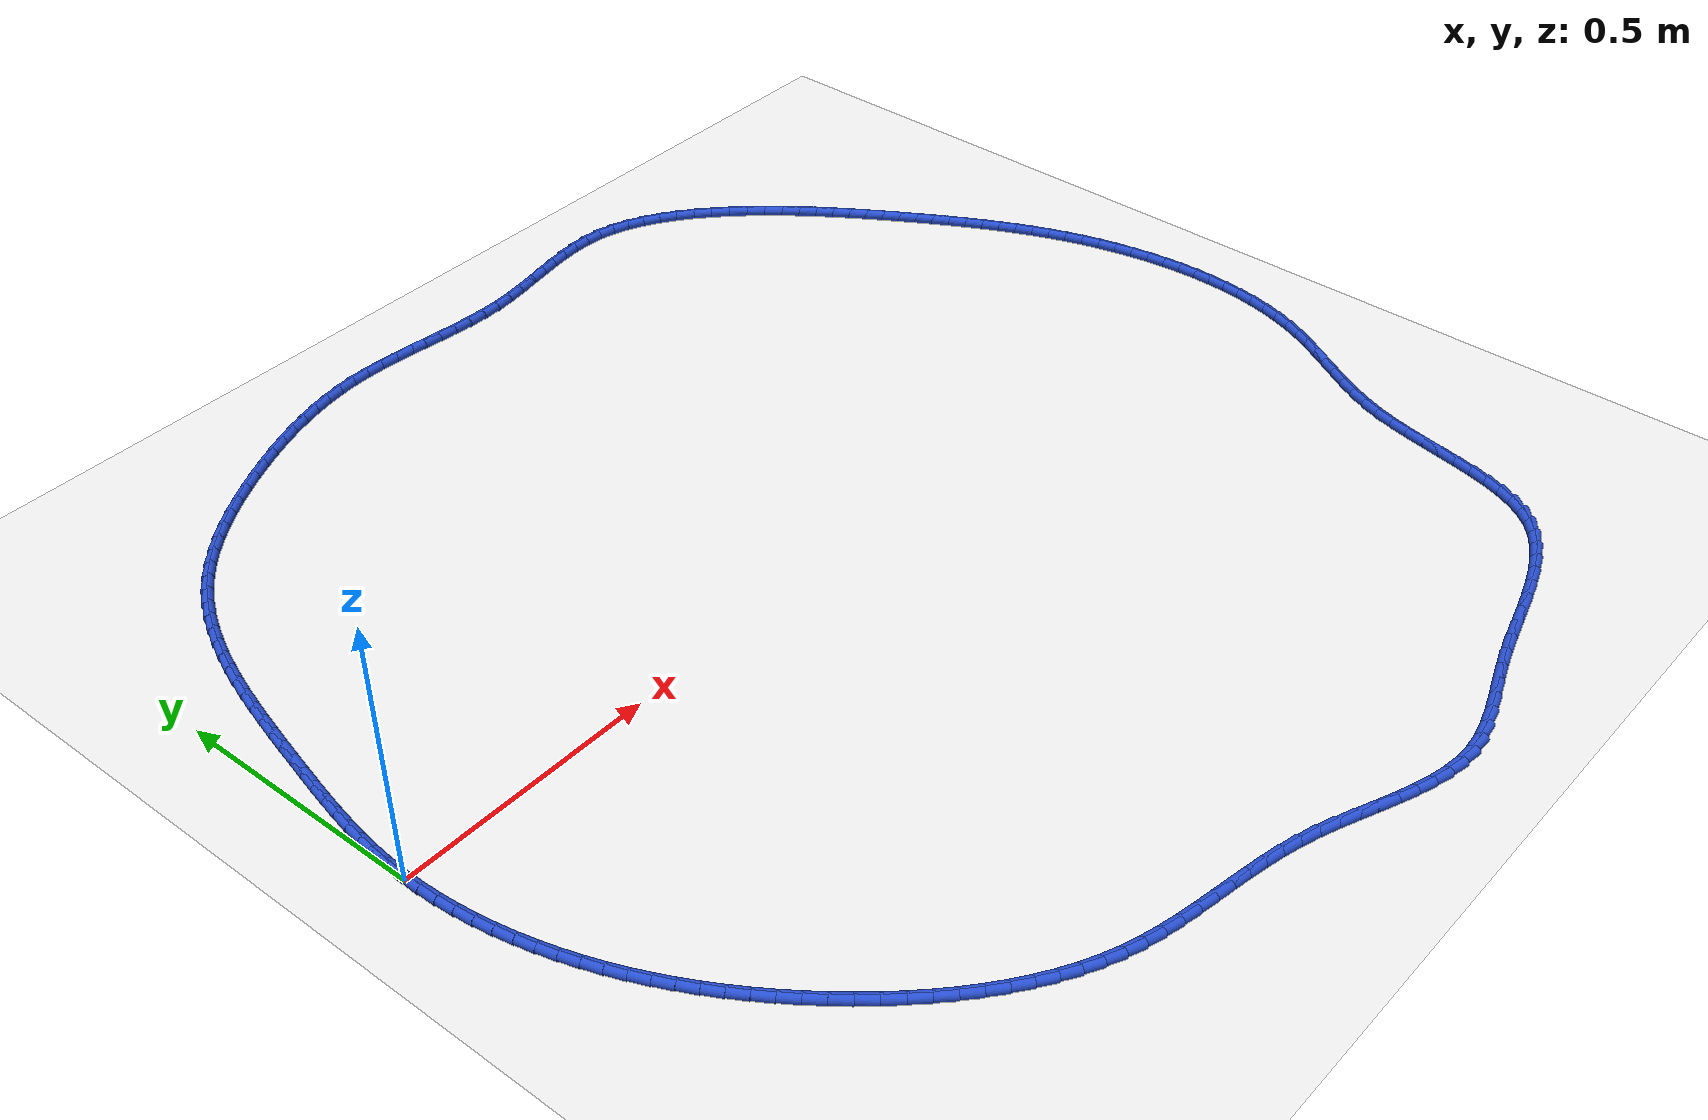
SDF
<sdf version="1.6">
 <world name="default">
  <light name="sun" type="directional">
   <pose>0 0 10 0 -0 0</pose>
   <diffuse>0.8 0.8 0.8 1</diffuse>
   <specular>0.2 0.2 0.2 1</specular>
   <attenuation>
    <range>1000</range>
    <constant>0.9</constant>
    <linear>0.01</linear>
    <quadratic>0.001</quadratic>
   </attenuation>
   <direction>-0.5 0.1 -0.9</direction>
  </light>
  <model name="ground_plane">
   <static>1</static>
   <link name="link">
    <collision name="collision">
     <geometry><plane><normal>0 0 1</normal><size>100 100</size></plane></geometry>
     <surface><friction><ode><mu>100</mu><mu2>50</mu2></ode></friction></surface>
    </collision>
    <visual name="visual">
     <cast_shadows>0</cast_shadows>
     <geometry><plane><normal>0 0 1</normal><size>100 100</size></plane></geometry>
     <material>
      <script><uri>file://media/materials/scripts/gazebo.material</uri><name>Gazebo/WhiteGlow</name></script>
     </material>
    </visual>
   </link>
  </model>
  <gravity>0 0 -9.8</gravity>
  <magnetic_field>6e-06 2.3e-05 -4.2e-05</magnetic_field>
  <atmosphere type="adiabatic"/>
  <physics name="default_physics" default="0" type="ode">
   <max_step_size>0.001</max_step_size>
   <real_time_factor>1</real_time_factor>
   <real_time_update_rate>1000</real_time_update_rate>
  </physics>
  <scene><ambient>0.4 0.4 0.4 1</ambient><background>0.7 0.7 0.7 1</background><shadows>1</shadows></scene>
  <spherical_coordinates>
   <surface_model>EARTH_WGS84</surface_model>
   <latitude_deg>0</latitude_deg>
   <longitude_deg>0</longitude_deg>
   <elevation>0</elevation>
   <heading_deg>0</heading_deg>
  </spherical_coordinates>
  <model name="line">
   <link name="link_0">
    <pose>3.469446951953614e-18 -6.938893903907228e-17 0.01 0 1.57 1.5252709959177169</pose>
    <collision name="collision">
     <geometry><cylinder><radius>0.01</radius><length>0.08</length></cylinder></geometry>
    </collision>
    <visual name="visual">
     <material>
      <script><name>Gazebo/Blue</name><uri>file://media/materials/scripts/gazebo.material</uri></script>
     </material>
     <geometry><cylinder><radius>0.01</radius><length>0.08</length></cylinder></geometry>
    </visual>
   </link>
   <link name="link_1">
    <pose>0.0016215854271124785 0.03559479888819767 0.01 0 1.57 1.4843025743258724</pose>
    <collision name="collision">
     <geometry><cylinder><radius>0.01</radius><length>0.08</length></cylinder></geometry>
    </collision>
    <visual name="visual">
     <material>
      <script><name>Gazebo/Blue</name><uri>file://media/materials/scripts/gazebo.material</uri></script>
     </material>
     <geometry><cylinder><radius>0.01</radius><length>0.08</length></cylinder></geometry>
    </visual>
   </link>
   <link name="link_2">
    <pose>0.004694859227865654 0.07103789153256174 0.01 0 1.57 1.448122174521788</pose>
    <collision name="collision">
     <geometry><cylinder><radius>0.01</radius><length>0.08</length></cylinder></geometry>
    </collision>
    <visual name="visual">
     <material>
      <script><name>Gazebo/Blue</name><uri>file://media/materials/scripts/gazebo.material</uri></script>
     </material>
     <geometry><cylinder><radius>0.01</radius><length>0.08</length></cylinder></geometry>
    </visual>
   </link>
   <link name="link_3">
    <pose>0.009051522361451635 0.1063736708929551 0.01 0 1.57 1.4168965451180486</pose>
    <collision name="collision">
     <geometry><cylinder><radius>0.01</radius><length>0.08</length></cylinder></geometry>
    </collision>
    <visual name="visual">
     <material>
      <script><name>Gazebo/Blue</name><uri>file://media/materials/scripts/gazebo.material</uri></script>
     </material>
     <geometry><cylinder><radius>0.01</radius><length>0.08</length></cylinder></geometry>
    </visual>
   </link>
   <link name="link_4">
    <pose>0.014523275787062528 0.14164652992924068 0.01 0 1.57 1.3907048843323373</pose>
    <collision name="collision">
     <geometry><cylinder><radius>0.01</radius><length>0.08</length></cylinder></geometry>
    </collision>
    <visual name="visual">
     <material>
      <script><name>Gazebo/Blue</name><uri>file://media/materials/scripts/gazebo.material</uri></script>
     </material>
     <geometry><cylinder><radius>0.01</radius><length>0.08</length></cylinder></geometry>
    </visual>
   </link>
   <link name="link_5">
    <pose>0.020941820463890454 0.1769008616012815 0.01 0 1.57 1.3695609450814363</pose>
    <collision name="collision">
     <geometry><cylinder><radius>0.01</radius><length>0.08</length></cylinder></geometry>
    </collision>
    <visual name="visual">
     <material>
      <script><name>Gazebo/Blue</name><uri>file://media/materials/scripts/gazebo.material</uri></script>
     </material>
     <geometry><cylinder><radius>0.01</radius><length>0.08</length></cylinder></geometry>
    </visual>
   </link>
   <link name="link_6">
    <pose>0.028138857351127516 0.21218105886894056 0.01 0 1.57 1.3534331985920862</pose>
    <collision name="collision">
     <geometry><cylinder><radius>0.01</radius><length>0.08</length></cylinder></geometry>
    </collision>
    <visual name="visual">
     <material>
      <script><name>Gazebo/Blue</name><uri>file://media/materials/scripts/gazebo.material</uri></script>
     </material>
     <geometry><cylinder><radius>0.01</radius><length>0.08</length></cylinder></geometry>
    </visual>
   </link>
   <link name="link_7">
    <pose>0.035946087407965795 0.24753151469208062 0.01 0 1.57 1.3422615743175024</pose>
    <collision name="collision">
     <geometry><cylinder><radius>0.01</radius><length>0.08</length></cylinder></geometry>
    </collision>
    <visual name="visual">
     <material>
      <script><name>Gazebo/Blue</name><uri>file://media/materials/scripts/gazebo.material</uri></script>
     </material>
     <geometry><cylinder><radius>0.01</radius><length>0.08</length></cylinder></geometry>
    </visual>
   </link>
   <link name="link_8">
    <pose>0.04419521159359743 0.28299662203056475 0.01 0 1.57 1.3359701525868268</pose>
    <collision name="collision">
     <geometry><cylinder><radius>0.01</radius><length>0.08</length></cylinder></geometry>
    </collision>
    <visual name="visual">
     <material>
      <script><name>Gazebo/Blue</name><uri>file://media/materials/scripts/gazebo.material</uri></script>
     </material>
     <geometry><cylinder><radius>0.01</radius><length>0.08</length></cylinder></geometry>
    </visual>
   </link>
   <link name="link_9">
    <pose>0.05271793086721454 0.318620773844256 0.01 0 1.57 1.3335910321006836</pose>
    <collision name="collision">
     <geometry><cylinder><radius>0.01</radius><length>0.08</length></cylinder></geometry>
    </collision>
    <visual name="visual">
     <material>
      <script><name>Gazebo/Blue</name><uri>file://media/materials/scripts/gazebo.material</uri></script>
     </material>
     <geometry><cylinder><radius>0.01</radius><length>0.08</length></cylinder></geometry>
    </visual>
   </link>
   <link name="link_10">
    <pose>0.06137551307065232 0.3544319178844713 0.01 0 1.57 1.3291348992225152</pose>
    <collision name="collision">
     <geometry><cylinder><radius>0.01</radius><length>0.08</length></cylinder></geometry>
    </collision>
    <visual name="visual">
     <material>
      <script><name>Gazebo/Blue</name><uri>file://media/materials/scripts/gazebo.material</uri></script>
     </material>
     <geometry><cylinder><radius>0.01</radius><length>0.08</length></cylinder></geometry>
    </visual>
   </link>
   <link name="link_11">
    <pose>0.07022792285595555 0.39034748600808084 0.01 0 1.57 1.3201595947029447</pose>
    <collision name="collision">
     <geometry><cylinder><radius>0.01</radius><length>0.08</length></cylinder></geometry>
    </collision>
    <visual name="visual">
     <material>
      <script><name>Gazebo/Blue</name><uri>file://media/materials/scripts/gazebo.material</uri></script>
     </material>
     <geometry><cylinder><radius>0.01</radius><length>0.08</length></cylinder></geometry>
    </visual>
   </link>
   <link name="link_12">
    <pose>0.07941697653739098 0.42623938387728244 0.01 0 1.57 1.3066158979692932</pose>
    <collision name="collision">
     <geometry><cylinder><radius>0.01</radius><length>0.08</length></cylinder></geometry>
    </collision>
    <visual name="visual">
     <material>
      <script><name>Gazebo/Blue</name><uri>file://media/materials/scripts/gazebo.material</uri></script>
     </material>
     <geometry><cylinder><radius>0.01</radius><length>0.08</length></cylinder></geometry>
    </visual>
   </link>
   <link name="link_13">
    <pose>0.0890847450197053 0.4619793755501151 0.01 0 1.57 1.2884036981123361</pose>
    <collision name="collision">
     <geometry><cylinder><radius>0.01</radius><length>0.08</length></cylinder></geometry>
    </collision>
    <visual name="visual">
     <material>
      <script><name>Gazebo/Blue</name><uri>file://media/materials/scripts/gazebo.material</uri></script>
     </material>
     <geometry><cylinder><radius>0.01</radius><length>0.08</length></cylinder></geometry>
    </visual>
   </link>
   <link name="link_14">
    <pose>0.09937329920764522 0.4974392250846179 0.01 0 1.57 1.265370862041352</pose>
    <collision name="collision">
     <geometry><cylinder><radius>0.01</radius><length>0.08</length></cylinder></geometry>
    </collision>
    <visual name="visual">
     <material>
      <script><name>Gazebo/Blue</name><uri>file://media/materials/scripts/gazebo.material</uri></script>
     </material>
     <geometry><cylinder><radius>0.01</radius><length>0.08</length></cylinder></geometry>
    </visual>
   </link>
   <link name="link_15">
    <pose>0.11042471000595751 0.5324906965388301 0.01 0 1.57 1.2373220945496048</pose>
    <collision name="collision">
     <geometry><cylinder><radius>0.01</radius><length>0.08</length></cylinder></geometry>
    </collision>
    <visual name="visual">
     <material>
      <script><name>Gazebo/Blue</name><uri>file://media/materials/scripts/gazebo.material</uri></script>
     </material>
     <geometry><cylinder><radius>0.01</radius><length>0.08</length></cylinder></geometry>
    </visual>
   </link>
   <link name="link_16">
    <pose>0.12238104831938887 0.5670055539707907 0.01 0 1.57 1.2040316661835129</pose>
    <collision name="collision">
     <geometry><cylinder><radius>0.01</radius><length>0.08</length></cylinder></geometry>
    </collision>
    <visual name="visual">
     <material>
      <script><name>Gazebo/Blue</name><uri>file://media/materials/scripts/gazebo.material</uri></script>
     </material>
     <geometry><cylinder><radius>0.01</radius><length>0.08</length></cylinder></geometry>
    </visual>
   </link>
   <link name="link_17">
    <pose>0.13538438505268607 0.6008555614385389 0.01 0 1.57 1.165261864110932</pose>
    <collision name="collision">
     <geometry><cylinder><radius>0.01</radius><length>0.08</length></cylinder></geometry>
    </collision>
    <visual name="visual">
     <material>
      <script><name>Gazebo/Blue</name><uri>file://media/materials/scripts/gazebo.material</uri></script>
     </material>
     <geometry><cylinder><radius>0.01</radius><length>0.08</length></cylinder></geometry>
    </visual>
   </link>
   <link name="link_18">
    <pose>0.14957679111059574 0.6339124830001137 0.01 0 1.57 1.1207892102602308</pose>
    <collision name="collision">
     <geometry><cylinder><radius>0.01</radius><length>0.08</length></cylinder></geometry>
    </collision>
    <visual name="visual">
     <material>
      <script><name>Gazebo/Blue</name><uri>file://media/materials/scripts/gazebo.material</uri></script>
     </material>
     <geometry><cylinder><radius>0.01</radius><length>0.08</length></cylinder></geometry>
    </visual>
   </link>
   <link name="link_19">
    <pose>0.16510033739786473 0.6660480827135544 0.01 0 1.57 1.0704402501146315</pose>
    <collision name="collision">
     <geometry><cylinder><radius>0.01</radius><length>0.08</length></cylinder></geometry>
    </collision>
    <visual name="visual">
     <material>
      <script><name>Gazebo/Blue</name><uri>file://media/materials/scripts/gazebo.material</uri></script>
     </material>
     <geometry><cylinder><radius>0.01</radius><length>0.08</length></cylinder></geometry>
    </visual>
   </link>
   <link name="link_20">
    <pose>0.1820970948192397 0.6971341246369 0.01 0 1.57 1.0141376483867708</pose>
    <collision name="collision">
     <geometry><cylinder><radius>0.01</radius><length>0.08</length></cylinder></geometry>
    </collision>
    <visual name="visual">
     <material>
      <script><name>Gazebo/Blue</name><uri>file://media/materials/scripts/gazebo.material</uri></script>
     </material>
     <geometry><cylinder><radius>0.01</radius><length>0.08</length></cylinder></geometry>
    </visual>
   </link>
   <link name="link_21">
    <pose>0.2007091342794674 0.7270423728281898 0.01 0 1.57 0.9519549781684653</pose>
    <collision name="collision">
     <geometry><cylinder><radius>0.01</radius><length>0.08</length></cylinder></geometry>
    </collision>
    <visual name="visual">
     <material>
      <script><name>Gazebo/Blue</name><uri>file://media/materials/scripts/gazebo.material</uri></script>
     </material>
     <geometry><cylinder><radius>0.01</radius><length>0.08</length></cylinder></geometry>
    </visual>
   </link>
   <link name="link_22">
    <pose>0.22107852668329459 0.7556445913454629 0.01 0 1.57 0.8842377619367613</pose>
    <collision name="collision">
     <geometry><cylinder><radius>0.01</radius><length>0.08</length></cylinder></geometry>
    </collision>
    <visual name="visual">
     <material>
      <script><name>Gazebo/Blue</name><uri>file://media/materials/scripts/gazebo.material</uri></script>
     </material>
     <geometry><cylinder><radius>0.01</radius><length>0.08</length></cylinder></geometry>
    </visual>
   </link>
   <link name="link_23">
    <pose>0.24334543017454585 0.7828137049964042 0.01 0 1.57 0.8153738039238577</pose>
    <collision name="collision">
     <geometry><cylinder><radius>0.01</radius><length>0.08</length></cylinder></geometry>
    </collision>
    <visual name="visual">
     <material>
      <script><name>Gazebo/Blue</name><uri>file://media/materials/scripts/gazebo.material</uri></script>
     </material>
     <geometry><cylinder><radius>0.01</radius><length>0.08</length></cylinder></geometry>
    </visual>
   </link>
   <link name="link_24">
    <pose>0.2675312133655589 0.8084947254371191 0.01 0 1.57 0.751770016367098</pose>
    <collision name="collision">
     <geometry><cylinder><radius>0.01</radius><length>0.08</length></cylinder></geometry>
    </collision>
    <visual name="visual">
     <material>
      <script><name>Gazebo/Blue</name><uri>file://media/materials/scripts/gazebo.material</uri></script>
     </material>
     <geometry><cylinder><radius>0.01</radius><length>0.08</length></cylinder></geometry>
    </visual>
   </link>
   <link name="link_25">
    <pose>0.29347076932197735 0.8327458261006809 0.01 0 1.57 0.6939370042739761</pose>
    <collision name="collision">
     <geometry><cylinder><radius>0.01</radius><length>0.08</length></cylinder></geometry>
    </collision>
    <visual name="visual">
     <material>
      <script><name>Gazebo/Blue</name><uri>file://media/materials/scripts/gazebo.material</uri></script>
     </material>
     <geometry><cylinder><radius>0.01</radius><length>0.08</length></cylinder></geometry>
    </visual>
   </link>
   <link name="link_26">
    <pose>0.3209826721498838 0.8556350835012648 0.01 0 1.57 0.6416911725735465</pose>
    <collision name="collision">
     <geometry><cylinder><radius>0.01</radius><length>0.08</length></cylinder></geometry>
    </collision>
    <visual name="visual">
     <material>
      <script><name>Gazebo/Blue</name><uri>file://media/materials/scripts/gazebo.material</uri></script>
     </material>
     <geometry><cylinder><radius>0.01</radius><length>0.08</length></cylinder></geometry>
    </visual>
   </link>
   <link name="link_27">
    <pose>0.3498854959553605 0.8772305741530455 0.01 0 1.57 0.594752475936522</pose>
    <collision name="collision">
     <geometry><cylinder><radius>0.01</radius><length>0.08</length></cylinder></geometry>
    </collision>
    <visual name="visual">
     <material>
      <script><name>Gazebo/Blue</name><uri>file://media/materials/scripts/gazebo.material</uri></script>
     </material>
     <geometry><cylinder><radius>0.01</radius><length>0.08</length></cylinder></geometry>
    </visual>
   </link>
   <link name="link_28">
    <pose>0.37999781484449 0.8976003745701978 0.01 0 1.57 0.5527924874781935</pose>
    <collision name="collision">
     <geometry><cylinder><radius>0.01</radius><length>0.08</length></cylinder></geometry>
    </collision>
    <visual name="visual">
     <material>
      <script><name>Gazebo/Blue</name><uri>file://media/materials/scripts/gazebo.material</uri></script>
     </material>
     <geometry><cylinder><radius>0.01</radius><length>0.08</length></cylinder></geometry>
    </visual>
   </link>
   <link name="link_29">
    <pose>0.41113820292335507 0.9168125612668966 0.01 0 1.57 0.5154700858104321</pose>
    <collision name="collision">
     <geometry><cylinder><radius>0.01</radius><length>0.08</length></cylinder></geometry>
    </collision>
    <visual name="visual">
     <material>
      <script><name>Gazebo/Blue</name><uri>file://media/materials/scripts/gazebo.material</uri></script>
     </material>
     <geometry><cylinder><radius>0.01</radius><length>0.08</length></cylinder></geometry>
    </visual>
   </link>
   <link name="link_30">
    <pose>0.4431252342980375 0.9349352107573163 0.01 0 1.57 0.482456335545518</pose>
    <collision name="collision">
     <geometry><cylinder><radius>0.01</radius><length>0.08</length></cylinder></geometry>
    </collision>
    <visual name="visual">
     <material>
      <script><name>Gazebo/Blue</name><uri>file://media/materials/scripts/gazebo.material</uri></script>
     </material>
     <geometry><cylinder><radius>0.01</radius><length>0.08</length></cylinder></geometry>
    </visual>
   </link>
   <link name="link_31">
    <pose>0.47577748307462053 0.9520363995556329 0.01 0 1.57 0.45329402082073994</pose>
    <collision name="collision">
     <geometry><cylinder><radius>0.01</radius><length>0.08</length></cylinder></geometry>
    </collision>
    <visual name="visual">
     <material>
      <script><name>Gazebo/Blue</name><uri>file://media/materials/scripts/gazebo.material</uri></script>
     </material>
     <geometry><cylinder><radius>0.01</radius><length>0.08</length></cylinder></geometry>
    </visual>
   </link>
   <link name="link_32">
    <pose>0.5089166664444291 0.968179298074831 0.01 0 1.57 0.4241555221904065</pose>
    <collision name="collision">
     <geometry><cylinder><radius>0.01</radius><length>0.08</length></cylinder></geometry>
    </collision>
    <visual name="visual">
     <material>
      <script><name>Gazebo/Blue</name><uri>file://media/materials/scripts/gazebo.material</uri></script>
     </material>
     <geometry><cylinder><radius>0.01</radius><length>0.08</length></cylinder></geometry>
    </visual>
   </link>
   <link name="link_33">
    <pose>0.542435990628355 0.9833154881498458 0.01 0 1.57 0.3912704653652923</pose>
    <collision name="collision">
     <geometry><cylinder><radius>0.01</radius><length>0.08</length></cylinder></geometry>
    </collision>
    <visual name="visual">
     <material>
      <script><name>Gazebo/Blue</name><uri>file://media/materials/scripts/gazebo.material</uri></script>
     </material>
     <geometry><cylinder><radius>0.01</radius><length>0.08</length></cylinder></geometry>
    </visual>
   </link>
   <link name="link_34">
    <pose>0.5762997081775405 0.9972856540552948 0.01 0 1.57 0.35425517601551254</pose>
    <collision name="collision">
     <geometry><cylinder><radius>0.01</radius><length>0.08</length></cylinder></geometry>
    </collision>
    <visual name="visual">
     <material>
      <script><name>Gazebo/Blue</name><uri>file://media/materials/scripts/gazebo.material</uri></script>
     </material>
     <geometry><cylinder><radius>0.01</radius><length>0.08</length></cylinder></geometry>
    </visual>
   </link>
   <link name="link_35">
    <pose>0.6104751261874367 1.0099257121698246 0.01 0 1.57 0.31287092518859894</pose>
    <collision name="collision">
     <geometry><cylinder><radius>0.01</radius><length>0.08</length></cylinder></geometry>
    </collision>
    <visual name="visual">
     <material>
      <script><name>Gazebo/Blue</name><uri>file://media/materials/scripts/gazebo.material</uri></script>
     </material>
     <geometry><cylinder><radius>0.01</radius><length>0.08</length></cylinder></geometry>
    </visual>
   </link>
   <link name="link_36">
    <pose>0.6449295517534953 1.0210715788720812 0.01 0 1.57 0.26688907058632577</pose>
    <collision name="collision">
     <geometry><cylinder><radius>0.01</radius><length>0.08</length></cylinder></geometry>
    </collision>
    <visual name="visual">
     <material>
      <script><name>Gazebo/Blue</name><uri>file://media/materials/scripts/gazebo.material</uri></script>
     </material>
     <geometry><cylinder><radius>0.01</radius><length>0.08</length></cylinder></geometry>
    </visual>
   </link>
   <link name="link_37">
    <pose>0.6796302919711666 1.0305591705407102 0.01 0 1.57 0.21611515996977596</pose>
    <collision name="collision">
     <geometry><cylinder><radius>0.01</radius><length>0.08</length></cylinder></geometry>
    </collision>
    <visual name="visual">
     <material>
      <script><name>Gazebo/Blue</name><uri>file://media/materials/scripts/gazebo.material</uri></script>
     </material>
     <geometry><cylinder><radius>0.01</radius><length>0.08</length></cylinder></geometry>
    </visual>
   </link>
   <link name="link_38">
    <pose>0.7145446539359029 1.0382244035543584 0.01 0 1.57 0.16042018617782255</pose>
    <collision name="collision">
     <geometry><cylinder><radius>0.01</radius><length>0.08</length></cylinder></geometry>
    </collision>
    <visual name="visual">
     <material>
      <script><name>Gazebo/Blue</name><uri>file://media/materials/scripts/gazebo.material</uri></script>
     </material>
     <geometry><cylinder><radius>0.01</radius><length>0.08</length></cylinder></geometry>
    </visual>
   </link>
   <link name="link_39">
    <pose>0.7496399447431552 1.0439031942916719 0.01 0 1.57 0.09977855602713531</pose>
    <collision name="collision">
     <geometry><cylinder><radius>0.01</radius><length>0.08</length></cylinder></geometry>
    </collision>
    <visual name="visual">
     <material>
      <script><name>Gazebo/Blue</name><uri>file://media/materials/scripts/gazebo.material</uri></script>
     </material>
     <geometry><cylinder><radius>0.01</radius><length>0.08</length></cylinder></geometry>
    </visual>
   </link>
   <link name="link_40">
    <pose>0.7848834714883745 1.0474314591312972 0.01 0 1.57 0.036308845575893534</pose>
    <collision name="collision">
     <geometry><cylinder><radius>0.01</radius><length>0.08</length></cylinder></geometry>
    </collision>
    <visual name="visual">
     <material>
      <script><name>Gazebo/Blue</name><uri>file://media/materials/scripts/gazebo.material</uri></script>
     </material>
     <geometry><cylinder><radius>0.01</radius><length>0.08</length></cylinder></geometry>
    </visual>
   </link>
   <link name="link_41">
    <pose>0.8202459848994611 1.0487159957015366 0.01 0 1.57 -0.018023304363358604</pose>
    <collision name="collision">
     <geometry><cylinder><radius>0.01</radius><length>0.08</length></cylinder></geometry>
    </collision>
    <visual name="visual">
     <material>
      <script><name>Gazebo/Blue</name><uri>file://media/materials/scripts/gazebo.material</uri></script>
     </material>
     <geometry><cylinder><radius>0.01</radius><length>0.08</length></cylinder></geometry>
    </visual>
   </link>
   <link name="link_42">
    <pose>0.8557183003638211 1.0480765981280873 0.01 0 1.57 -0.058795400048411085</pose>
    <collision name="collision">
     <geometry><cylinder><radius>0.01</radius><length>0.08</length></cylinder></geometry>
    </collision>
    <visual name="visual">
     <material>
      <script><name>Gazebo/Blue</name><uri>file://media/materials/scripts/gazebo.material</uri></script>
     </material>
     <geometry><cylinder><radius>0.01</radius><length>0.08</length></cylinder></geometry>
    </visual>
   </link>
   <link name="link_43">
    <pose>0.8912984805479177 1.0459822333080777 0.01 0 1.57 -0.08609924251803423</pose>
    <collision name="collision">
     <geometry><cylinder><radius>0.01</radius><length>0.08</length></cylinder></geometry>
    </collision>
    <visual name="visual">
     <material>
      <script><name>Gazebo/Blue</name><uri>file://media/materials/scripts/gazebo.material</uri></script>
     </material>
     <geometry><cylinder><radius>0.01</radius><length>0.08</length></cylinder></geometry>
    </visual>
   </link>
   <link name="link_44">
    <pose>0.9269845979594197 1.0429020707029173 0.01 0 1.57 -0.10016044524635809</pose>
    <collision name="collision">
     <geometry><cylinder><radius>0.01</radius><length>0.08</length></cylinder></geometry>
    </collision>
    <visual name="visual">
     <material>
      <script><name>Gazebo/Blue</name><uri>file://media/materials/scripts/gazebo.material</uri></script>
     </material>
     <geometry><cylinder><radius>0.01</radius><length>0.08</length></cylinder></geometry>
    </visual>
   </link>
   <link name="link_45">
    <pose>0.9627747251059957 1.039305279774016 0.01 0 1.57 -0.10118641085470102</pose>
    <collision name="collision">
     <geometry><cylinder><radius>0.01</radius><length>0.08</length></cylinder></geometry>
    </collision>
    <visual name="visual">
     <material>
      <script><name>Gazebo/Blue</name><uri>file://media/materials/scripts/gazebo.material</uri></script>
     </material>
     <geometry><cylinder><radius>0.01</radius><length>0.08</length></cylinder></geometry>
    </visual>
   </link>
   <link name="link_46">
    <pose>0.9986669344953145 1.035661029982783 0.01 0 1.57 -0.08929586787570433</pose>
    <collision name="collision">
     <geometry><cylinder><radius>0.01</radius><length>0.08</length></cylinder></geometry>
    </collision>
    <visual name="visual">
     <material>
      <script><name>Gazebo/Blue</name><uri>file://media/materials/scripts/gazebo.material</uri></script>
     </material>
     <geometry><cylinder><radius>0.01</radius><length>0.08</length></cylinder></geometry>
    </visual>
   </link>
   <link name="link_47">
    <pose>1.0346592986350442 1.0324384907906283 0.01 0 1.57 -0.06451607201602601</pose>
    <collision name="collision">
     <geometry><cylinder><radius>0.01</radius><length>0.08</length></cylinder></geometry>
    </collision>
    <visual name="visual">
     <material>
      <script><name>Gazebo/Blue</name><uri>file://media/materials/scripts/gazebo.material</uri></script>
     </material>
     <geometry><cylinder><radius>0.01</radius><length>0.08</length></cylinder></geometry>
    </visual>
   </link>
   <link name="link_48">
    <pose>1.0707498900328543 1.0301068316589612 0.01 0 1.57 -0.026843318075817264</pose>
    <collision name="collision">
     <geometry><cylinder><radius>0.01</radius><length>0.08</length></cylinder></geometry>
    </collision>
    <visual name="visual">
     <material>
      <script><name>Gazebo/Blue</name><uri>file://media/materials/scripts/gazebo.material</uri></script>
     </material>
     <geometry><cylinder><radius>0.01</radius><length>0.08</length></cylinder></geometry>
    </visual>
   </link>
   <link name="link_49">
    <pose>1.1069367811964124 1.0291352220491916 0.01 0 1.57 0.0236334024040405</pose>
    <collision name="collision">
     <geometry><cylinder><radius>0.01</radius><length>0.08</length></cylinder></geometry>
    </collision>
    <visual name="visual">
     <material>
      <script><name>Gazebo/Blue</name><uri>file://media/materials/scripts/gazebo.material</uri></script>
     </material>
     <geometry><cylinder><radius>0.01</radius><length>0.08</length></cylinder></geometry>
    </visual>
   </link>
   <link name="link_50">
    <pose>1.1432180446333882 1.0299928314227287 0.01 0 1.57 0.08557054927857073</pose>
    <collision name="collision">
     <geometry><cylinder><radius>0.01</radius><length>0.08</length></cylinder></geometry>
    </collision>
    <visual name="visual">
     <material>
      <script><name>Gazebo/Blue</name><uri>file://media/materials/scripts/gazebo.material</uri></script>
     </material>
     <geometry><cylinder><radius>0.01</radius><length>0.08</length></cylinder></geometry>
    </visual>
   </link>
   <link name="link_51">
    <pose>1.1795893372511213 1.033112761671324 0.01 0 1.57 0.14087808753635053</pose>
    <collision name="collision">
     <geometry><cylinder><radius>0.01</radius><length>0.08</length></cylinder></geometry>
    </collision>
    <visual name="visual">
     <material>
      <script><name>Gazebo/Blue</name><uri>file://media/materials/scripts/gazebo.material</uri></script>
     </material>
     <geometry><cylinder><radius>0.01</radius><length>0.08</length></cylinder></geometry>
    </visual>
   </link>
   <link name="link_52">
    <pose>1.2160026955651086 1.0382768142616234 0.01 0 1.57 0.17484324159611364</pose>
    <collision name="collision">
     <geometry><cylinder><radius>0.01</radius><length>0.08</length></cylinder></geometry>
    </collision>
    <visual name="visual">
     <material>
      <script><name>Gazebo/Blue</name><uri>file://media/materials/scripts/gazebo.material</uri></script>
     </material>
     <geometry><cylinder><radius>0.01</radius><length>0.08</length></cylinder></geometry>
    </visual>
   </link>
   <link name="link_53">
    <pose>1.2523722889411137 1.0447013924673783 0.01 0 1.57 0.18769182467498893</pose>
    <collision name="collision">
     <geometry><cylinder><radius>0.01</radius><length>0.08</length></cylinder></geometry>
    </collision>
    <visual name="visual">
     <material>
      <script><name>Gazebo/Blue</name><uri>file://media/materials/scripts/gazebo.material</uri></script>
     </material>
     <geometry><cylinder><radius>0.01</radius><length>0.08</length></cylinder></geometry>
    </visual>
   </link>
   <link name="link_54">
    <pose>1.2886110290138513 1.0515841202545013 0.01 0 1.57 0.1795650061260152</pose>
    <collision name="collision">
     <geometry><cylinder><radius>0.01</radius><length>0.08</length></cylinder></geometry>
    </collision>
    <visual name="visual">
     <material>
      <script><name>Gazebo/Blue</name><uri>file://media/materials/scripts/gazebo.material</uri></script>
     </material>
     <geometry><cylinder><radius>0.01</radius><length>0.08</length></cylinder></geometry>
    </visual>
   </link>
   <link name="link_55">
    <pose>1.3246318274180358 1.058122621588905 0.01 0 1.57 0.14983543711533862</pose>
    <collision name="collision">
     <geometry><cylinder><radius>0.01</radius><length>0.08</length></cylinder></geometry>
    </collision>
    <visual name="visual">
     <material>
      <script><name>Gazebo/Blue</name><uri>file://media/materials/scripts/gazebo.material</uri></script>
     </material>
     <geometry><cylinder><radius>0.01</radius><length>0.08</length></cylinder></geometry>
    </visual>
   </link>
   <link name="link_56">
    <pose>1.36034759578838 1.0635145204365009 0.01 0 1.57 0.09716095291829273</pose>
    <collision name="collision">
     <geometry><cylinder><radius>0.01</radius><length>0.08</length></cylinder></geometry>
    </collision>
    <visual name="visual">
     <material>
      <script><name>Gazebo/Blue</name><uri>file://media/materials/scripts/gazebo.material</uri></script>
     </material>
     <geometry><cylinder><radius>0.01</radius><length>0.08</length></cylinder></geometry>
    </visual>
   </link>
   <link name="link_57">
    <pose>1.3956712457596 1.0669574407632019 0.01 0 1.57 0.01984462726434598</pose>
    <collision name="collision">
     <geometry><cylinder><radius>0.01</radius><length>0.08</length></cylinder></geometry>
    </collision>
    <visual name="visual">
     <material>
      <script><name>Gazebo/Blue</name><uri>file://media/materials/scripts/gazebo.material</uri></script>
     </material>
     <geometry><cylinder><radius>0.01</radius><length>0.08</length></cylinder></geometry>
    </visual>
   </link>
   <link name="link_58">
    <pose>1.4305156889664097 1.0676490065349198 0.01 0 1.57 -0.08330499272874595</pose>
    <collision name="collision">
     <geometry><cylinder><radius>0.01</radius><length>0.08</length></cylinder></geometry>
    </collision>
    <visual name="visual">
     <material>
      <script><name>Gazebo/Blue</name><uri>file://media/materials/scripts/gazebo.material</uri></script>
     </material>
     <geometry><cylinder><radius>0.01</radius><length>0.08</length></cylinder></geometry>
    </visual>
   </link>
   <link name="link_59">
    <pose>1.464793837043523 1.064786841717567 0.01 0 1.57 -0.20657104194303194</pose>
    <collision name="collision">
     <geometry><cylinder><radius>0.01</radius><length>0.08</length></cylinder></geometry>
    </collision>
    <visual name="visual">
     <material>
      <script><name>Gazebo/Blue</name><uri>file://media/materials/scripts/gazebo.material</uri></script>
     </material>
     <geometry><cylinder><radius>0.01</radius><length>0.08</length></cylinder></geometry>
    </visual>
   </link>
   <link name="link_60">
    <pose>1.4984221178338086 1.0577396886436585 0.01 0 1.57 -0.3241474964615592</pose>
    <collision name="collision">
     <geometry><cylinder><radius>0.01</radius><length>0.08</length></cylinder></geometry>
    </collision>
    <visual name="visual">
     <material>
      <script><name>Gazebo/Blue</name><uri>file://media/materials/scripts/gazebo.material</uri></script>
     </material>
     <geometry><cylinder><radius>0.01</radius><length>0.08</length></cylinder></geometry>
    </visual>
   </link>
   <link name="link_61">
    <pose>1.5313335050466685 1.0466815041070565 0.01 0 1.57 -0.4279942505644177</pose>
    <collision name="collision">
     <geometry><cylinder><radius>0.01</radius><length>0.08</length></cylinder></geometry>
    </collision>
    <visual name="visual">
     <material>
      <script><name>Gazebo/Blue</name><uri>file://media/materials/scripts/gazebo.material</uri></script>
     </material>
     <geometry><cylinder><radius>0.01</radius><length>0.08</length></cylinder></geometry>
    </visual>
   </link>
   <link name="link_62">
    <pose>1.5634658347777493 1.032022875827801 0.01 0 1.57 -0.5183704773376845</pose>
    <collision name="collision">
     <geometry><cylinder><radius>0.01</radius><length>0.08</length></cylinder></geometry>
    </collision>
    <visual name="visual">
     <material>
      <script><name>Gazebo/Blue</name><uri>file://media/materials/scripts/gazebo.material</uri></script>
     </material>
     <geometry><cylinder><radius>0.01</radius><length>0.08</length></cylinder></geometry>
    </visual>
   </link>
   <link name="link_63">
    <pose>1.5947569437790723 1.0141744234687957 0.01 0 1.57 -0.5963661973946723</pose>
    <collision name="collision">
     <geometry><cylinder><radius>0.01</radius><length>0.08</length></cylinder></geometry>
    </collision>
    <visual name="visual">
     <material>
      <script><name>Gazebo/Blue</name><uri>file://media/materials/scripts/gazebo.material</uri></script>
     </material>
     <geometry><cylinder><radius>0.01</radius><length>0.08</length></cylinder></geometry>
    </visual>
   </link>
   <link name="link_64">
    <pose>1.6251446688026607 0.9935467666929443 0.01 0 1.57 -0.6634175011654742</pose>
    <collision name="collision">
     <geometry><cylinder><radius>0.01</radius><length>0.08</length></cylinder></geometry>
    </collision>
    <visual name="visual">
     <material>
      <script><name>Gazebo/Blue</name><uri>file://media/materials/scripts/gazebo.material</uri></script>
     </material>
     <geometry><cylinder><radius>0.01</radius><length>0.08</length></cylinder></geometry>
    </visual>
   </link>
   <link name="link_65">
    <pose>1.6545668466005354 0.9705505251631504 0.01 0 1.57 -0.7210009900164638</pose>
    <collision name="collision">
     <geometry><cylinder><radius>0.01</radius><length>0.08</length></cylinder></geometry>
    </collision>
    <visual name="visual">
     <material>
      <script><name>Gazebo/Blue</name><uri>file://media/materials/scripts/gazebo.material</uri></script>
     </material>
     <geometry><cylinder><radius>0.01</radius><length>0.08</length></cylinder></geometry>
    </visual>
   </link>
   <link name="link_66">
    <pose>1.6829613139247181 0.9455963185423178 0.01 0 1.57 -0.7704745533394818</pose>
    <collision name="collision">
     <geometry><cylinder><radius>0.01</radius><length>0.08</length></cylinder></geometry>
    </collision>
    <visual name="visual">
     <material>
      <script><name>Gazebo/Blue</name><uri>file://media/materials/scripts/gazebo.material</uri></script>
     </material>
     <geometry><cylinder><radius>0.01</radius><length>0.08</length></cylinder></geometry>
    </visual>
   </link>
   <link name="link_67">
    <pose>1.7102659075272315 0.9190947664933501 0.01 0 1.57 -0.8130114837493991</pose>
    <collision name="collision">
     <geometry><cylinder><radius>0.01</radius><length>0.08</length></cylinder></geometry>
    </collision>
    <visual name="visual">
     <material>
      <script><name>Gazebo/Blue</name><uri>file://media/materials/scripts/gazebo.material</uri></script>
     </material>
     <geometry><cylinder><radius>0.01</radius><length>0.08</length></cylinder></geometry>
    </visual>
   </link>
   <link name="link_68">
    <pose>1.7364184641600964 0.8914564886791505 0.01 0 1.57 -0.8495847549773512</pose>
    <collision name="collision">
     <geometry><cylinder><radius>0.01</radius><length>0.08</length></cylinder></geometry>
    </collision>
    <visual name="visual">
     <material>
      <script><name>Gazebo/Blue</name><uri>file://media/materials/scripts/gazebo.material</uri></script>
     </material>
     <geometry><cylinder><radius>0.01</radius><length>0.08</length></cylinder></geometry>
    </visual>
   </link>
   <link name="link_69">
    <pose>1.7613568205753358 0.8630921047626233 0.01 0 1.57 -0.881142298969791</pose>
    <collision name="collision">
     <geometry><cylinder><radius>0.01</radius><length>0.08</length></cylinder></geometry>
    </collision>
    <visual name="visual">
     <material>
      <script><name>Gazebo/Blue</name><uri>file://media/materials/scripts/gazebo.material</uri></script>
     </material>
     <geometry><cylinder><radius>0.01</radius><length>0.08</length></cylinder></geometry>
    </visual>
   </link>
   <link name="link_70">
    <pose>1.7850329853172557 0.8343851852936323 0.01 0 1.57 -0.9095995115521214</pose>
    <collision name="collision">
     <geometry><cylinder><radius>0.01</radius><length>0.08</length></cylinder></geometry>
    </collision>
    <visual name="visual">
     <material>
      <script><name>Gazebo/Blue</name><uri>file://media/materials/scripts/gazebo.material</uri></script>
     </material>
     <geometry><cylinder><radius>0.01</radius><length>0.08</length></cylinder></geometry>
    </visual>
   </link>
   <link name="link_71">
    <pose>1.8075293303576023 0.805470481546821 0.01 0 1.57 -0.9355253372611784</pose>
    <collision name="collision">
     <geometry><cylinder><radius>0.01</radius><length>0.08</length></cylinder></geometry>
    </collision>
    <visual name="visual">
     <material>
      <script><name>Gazebo/Blue</name><uri>file://media/materials/scripts/gazebo.material</uri></script>
     </material>
     <geometry><cylinder><radius>0.01</radius><length>0.08</length></cylinder></geometry>
    </visual>
   </link>
   <link name="link_72">
    <pose>1.8289984458975121 0.7763487221703389 0.01 0 1.57 -0.958593942592003</pose>
    <collision name="collision">
     <geometry><cylinder><radius>0.01</radius><length>0.08</length></cylinder></geometry>
    </collision>
    <visual name="visual">
     <material>
      <script><name>Gazebo/Blue</name><uri>file://media/materials/scripts/gazebo.material</uri></script>
     </material>
     <geometry><cylinder><radius>0.01</radius><length>0.08</length></cylinder></geometry>
    </visual>
   </link>
   <link name="link_73">
    <pose>1.8495936014610201 0.7470193392168464 0.01 0 1.57 -0.9785226420606887</pose>
    <collision name="collision">
     <geometry><cylinder><radius>0.01</radius><length>0.08</length></cylinder></geometry>
    </collision>
    <visual name="visual">
     <material>
      <script><name>Gazebo/Blue</name><uri>file://media/materials/scripts/gazebo.material</uri></script>
     </material>
     <geometry><cylinder><radius>0.01</radius><length>0.08</length></cylinder></geometry>
    </visual>
   </link>
   <link name="link_74">
    <pose>1.869468066572165 0.7174817647390028 0.01 0 1.57 -0.9950848318094315</pose>
    <collision name="collision">
     <geometry><cylinder><radius>0.01</radius><length>0.08</length></cylinder></geometry>
    </collision>
    <visual name="visual">
     <material>
      <script><name>Gazebo/Blue</name><uri>file://media/materials/scripts/gazebo.material</uri></script>
     </material>
     <geometry><cylinder><radius>0.01</radius><length>0.08</length></cylinder></geometry>
    </visual>
   </link>
   <link name="link_75">
    <pose>1.8887751107549846 0.6877354307894687 0.01 0 1.57 -1.0081120430420631</pose>
    <collision name="collision">
     <geometry><cylinder><radius>0.01</radius><length>0.08</length></cylinder></geometry>
    </collision>
    <visual name="visual">
     <material>
      <script><name>Gazebo/Blue</name><uri>file://media/materials/scripts/gazebo.material</uri></script>
     </material>
     <geometry><cylinder><radius>0.01</radius><length>0.08</length></cylinder></geometry>
    </visual>
   </link>
   <link name="link_76">
    <pose>1.9076680035335145 0.6577797694209045 0.01 0 1.57 -1.0174957932902071</pose>
    <collision name="collision">
     <geometry><cylinder><radius>0.01</radius><length>0.08</length></cylinder></geometry>
    </collision>
    <visual name="visual">
     <material>
      <script><name>Gazebo/Blue</name><uri>file://media/materials/scripts/gazebo.material</uri></script>
     </material>
     <geometry><cylinder><radius>0.01</radius><length>0.08</length></cylinder></geometry>
    </visual>
   </link>
   <link name="link_77">
    <pose>1.926299937012933 0.6276142007577151 0.01 0 1.57 -1.0247477678182646</pose>
    <collision name="collision">
     <geometry><cylinder><radius>0.01</radius><length>0.08</length></cylinder></geometry>
    </collision>
    <visual name="visual">
     <material>
      <script><name>Gazebo/Blue</name><uri>file://media/materials/scripts/gazebo.material</uri></script>
     </material>
     <geometry><cylinder><radius>0.01</radius><length>0.08</length></cylinder></geometry>
    </visual>
   </link>
   <link name="link_78">
    <pose>1.944764487283188 0.5972289596303455 0.01 0 1.57 -1.0342119913672487</pose>
    <collision name="collision">
     <geometry><cylinder><radius>0.01</radius><length>0.08</length></cylinder></geometry>
    </collision>
    <visual name="visual">
     <material>
      <script><name>Gazebo/Blue</name><uri>file://media/materials/scripts/gazebo.material</uri></script>
     </material>
     <geometry><cylinder><radius>0.01</radius><length>0.08</length></cylinder></geometry>
    </visual>
   </link>
   <link name="link_79">
    <pose>1.962989195480705 0.5665886991551644 0.01 0 1.57 -1.0466310420004505</pose>
    <collision name="collision">
     <geometry><cylinder><radius>0.01</radius><length>0.08</length></cylinder></geometry>
    </collision>
    <visual name="visual">
     <material>
      <script><name>Gazebo/Blue</name><uri>file://media/materials/scripts/gazebo.material</uri></script>
     </material>
     <geometry><cylinder><radius>0.01</radius><length>0.08</length></cylinder></geometry>
    </visual>
   </link>
   <link name="link_80">
    <pose>1.9808729263379492 0.5356536541525658 0.01 0 1.57 -1.0619980623714014</pose>
    <collision name="collision">
     <geometry><cylinder><radius>0.01</radius><length>0.08</length></cylinder></geometry>
    </collision>
    <visual name="visual">
     <material>
      <script><name>Gazebo/Blue</name><uri>file://media/materials/scripts/gazebo.material</uri></script>
     </material>
     <geometry><cylinder><radius>0.01</radius><length>0.08</length></cylinder></geometry>
    </visual>
   </link>
   <link name="link_81">
    <pose>1.9983145445873887 0.5043840594429433 0.01 0 1.57 -1.0803072613480527</pose>
    <collision name="collision">
     <geometry><cylinder><radius>0.01</radius><length>0.08</length></cylinder></geometry>
    </collision>
    <visual name="visual">
     <material>
      <script><name>Gazebo/Blue</name><uri>file://media/materials/scripts/gazebo.material</uri></script>
     </material>
     <geometry><cylinder><radius>0.01</radius><length>0.08</length></cylinder></geometry>
    </visual>
   </link>
   <link name="link_82">
    <pose>2.015212914961491 0.47274014984669144 0.01 0 1.57 -1.1015498589501629</pose>
    <collision name="collision">
     <geometry><cylinder><radius>0.01</radius><length>0.08</length></cylinder></geometry>
    </collision>
    <visual name="visual">
     <material>
      <script><name>Gazebo/Blue</name><uri>file://media/materials/scripts/gazebo.material</uri></script>
     </material>
     <geometry><cylinder><radius>0.01</radius><length>0.08</length></cylinder></geometry>
    </visual>
   </link>
   <link name="link_83">
    <pose>2.0314669021927214 0.4406821601842041 0.01 0 1.57 -1.125709327581201</pose>
    <collision name="collision">
     <geometry><cylinder><radius>0.01</radius><length>0.08</length></cylinder></geometry>
    </collision>
    <visual name="visual">
     <material>
      <script><name>Gazebo/Blue</name><uri>file://media/materials/scripts/gazebo.material</uri></script>
     </material>
     <geometry><cylinder><radius>0.01</radius><length>0.08</length></cylinder></geometry>
    </visual>
   </link>
   <link name="link_84">
    <pose>2.0469753710135485 0.40817032527587505 0.01 0 1.57 -1.1527559885985998</pose>
    <collision name="collision">
     <geometry><cylinder><radius>0.01</radius><length>0.08</length></cylinder></geometry>
    </collision>
    <visual name="visual">
     <material>
      <script><name>Gazebo/Blue</name><uri>file://media/materials/scripts/gazebo.material</uri></script>
     </material>
     <geometry><cylinder><radius>0.01</radius><length>0.08</length></cylinder></geometry>
    </visual>
   </link>
   <link name="link_85">
    <pose>2.0616371861564384 0.3751648799420984 0.01 0 1.57 -1.182641100235529</pose>
    <collision name="collision">
     <geometry><cylinder><radius>0.01</radius><length>0.08</length></cylinder></geometry>
    </collision>
    <visual name="visual">
     <material>
      <script><name>Gazebo/Blue</name><uri>file://media/materials/scripts/gazebo.material</uri></script>
     </material>
     <geometry><cylinder><radius>0.01</radius><length>0.08</length></cylinder></geometry>
    </visual>
   </link>
   <link name="link_86">
    <pose>2.0753512123538576 0.34162605900326853 0.01 0 1.57 -1.2152906776699097</pose>
    <collision name="collision">
     <geometry><cylinder><radius>0.01</radius><length>0.08</length></cylinder></geometry>
    </collision>
    <visual name="visual">
     <material>
      <script><name>Gazebo/Blue</name><uri>file://media/materials/scripts/gazebo.material</uri></script>
     </material>
     <geometry><cylinder><radius>0.01</radius><length>0.08</length></cylinder></geometry>
    </visual>
   </link>
   <link name="link_87">
    <pose>2.0880163143382746 0.307514097279779 0.01 0 1.57 -1.2505994121437427</pose>
    <collision name="collision">
     <geometry><cylinder><radius>0.01</radius><length>0.08</length></cylinder></geometry>
    </collision>
    <visual name="visual">
     <material>
      <script><name>Gazebo/Blue</name><uri>file://media/materials/scripts/gazebo.material</uri></script>
     </material>
     <geometry><cylinder><radius>0.01</radius><length>0.08</length></cylinder></geometry>
    </visual>
   </link>
   <link name="link_88">
    <pose>2.099531356842155 0.27278922959202395 0.01 0 1.57 -1.2882680253399197</pose>
    <collision name="collision">
     <geometry><cylinder><radius>0.01</radius><length>0.08</length></cylinder></geometry>
    </collision>
    <visual name="visual">
     <material>
      <script><name>Gazebo/Blue</name><uri>file://media/materials/scripts/gazebo.material</uri></script>
     </material>
     <geometry><cylinder><radius>0.01</radius><length>0.08</length></cylinder></geometry>
    </visual>
   </link>
   <link name="link_89">
    <pose>2.1097978652505014 0.237423291607962 0.01 0 1.57 -1.3269212375857353</pose>
    <collision name="collision">
     <geometry><cylinder><radius>0.01</radius><length>0.08</length></cylinder></geometry>
    </collision>
    <visual name="visual">
     <material>
      <script><name>Gazebo/Blue</name><uri>file://media/materials/scripts/gazebo.material</uri></script>
     </material>
     <geometry><cylinder><radius>0.01</radius><length>0.08</length></cylinder></geometry>
    </visual>
   </link>
   <link name="link_90">
    <pose>2.1187399327188383 0.20148651788913038 0.01 0 1.57 -1.3661304447037097</pose>
    <collision name="collision">
     <geometry><cylinder><radius>0.01</radius><length>0.08</length></cylinder></geometry>
    </collision>
    <visual name="visual">
     <material>
      <script><name>Gazebo/Blue</name><uri>file://media/materials/scripts/gazebo.material</uri></script>
     </material>
     <geometry><cylinder><radius>0.01</radius><length>0.08</length></cylinder></geometry>
    </visual>
   </link>
   <link name="link_91">
    <pose>2.12629302706866 0.16509873826146876 0.01 0 1.57 -1.4061799589978192</pose>
    <collision name="collision">
     <geometry><cylinder><radius>0.01</radius><length>0.08</length></cylinder></geometry>
    </collision>
    <visual name="visual">
     <material>
      <script><name>Gazebo/Blue</name><uri>file://media/materials/scripts/gazebo.material</uri></script>
     </material>
     <geometry><cylinder><radius>0.01</radius><length>0.08</length></cylinder></geometry>
    </visual>
   </link>
   <link name="link_92">
    <pose>2.132392703046546 0.128380161557449 0.01 0 1.57 -1.4473568395732224</pose>
    <collision name="collision">
     <geometry><cylinder><radius>0.01</radius><length>0.08</length></cylinder></geometry>
    </collision>
    <visual name="visual">
     <material>
      <script><name>Gazebo/Blue</name><uri>file://media/materials/scripts/gazebo.material</uri></script>
     </material>
     <geometry><cylinder><radius>0.01</radius><length>0.08</length></cylinder></geometry>
    </visual>
   </link>
   <link name="link_93">
    <pose>2.1369745153990767 0.0914509966095431 0.01 0 1.57 -1.4899480797754947</pose>
    <collision name="collision">
     <geometry><cylinder><radius>0.01</radius><length>0.08</length></cylinder></geometry>
    </collision>
    <visual name="visual">
     <material>
      <script><name>Gazebo/Blue</name><uri>file://media/materials/scripts/gazebo.material</uri></script>
     </material>
     <geometry><cylinder><radius>0.01</radius><length>0.08</length></cylinder></geometry>
    </visual>
   </link>
   <link name="link_94">
    <pose>2.1399740188728313 0.054431452250221765 0.01 0 1.57 -1.5342416586703944</pose>
    <collision name="collision">
     <geometry><cylinder><radius>0.01</radius><length>0.08</length></cylinder></geometry>
    </collision>
    <visual name="visual">
     <material>
      <script><name>Gazebo/Blue</name><uri>file://media/materials/scripts/gazebo.material</uri></script>
     </material>
     <geometry><cylinder><radius>0.01</radius><length>0.08</length></cylinder></geometry>
    </visual>
   </link>
   <link name="link_95">
    <pose>2.1413267682143915 0.01744173731195696 0.01 0 1.57 1.5610666341069936</pose>
    <collision name="collision">
     <geometry><cylinder><radius>0.01</radius><length>0.08</length></cylinder></geometry>
    </collision>
    <visual name="visual">
     <material>
      <script><name>Gazebo/Blue</name><uri>file://media/materials/scripts/gazebo.material</uri></script>
     </material>
     <geometry><cylinder><radius>0.01</radius><length>0.08</length></cylinder></geometry>
    </visual>
   </link>
   <link name="link_96">
    <pose>2.1409683181703354 -0.019397939372779786 0.01 0 1.57 1.5125050973401726</pose>
    <collision name="collision">
     <geometry><cylinder><radius>0.01</radius><length>0.08</length></cylinder></geometry>
    </collision>
    <visual name="visual">
     <material>
      <script><name>Gazebo/Blue</name><uri>file://media/materials/scripts/gazebo.material</uri></script>
     </material>
     <geometry><cylinder><radius>0.01</radius><length>0.08</length></cylinder></geometry>
    </visual>
   </link>
   <link name="link_97">
    <pose>2.1388342234872457 -0.05596736897151691 0.01 0 1.57 1.4613870761054026</pose>
    <collision name="collision">
     <geometry><cylinder><radius>0.01</radius><length>0.08</length></cylinder></geometry>
    </collision>
    <visual name="visual">
     <material>
      <script><name>Gazebo/Blue</name><uri>file://media/materials/scripts/gazebo.material</uri></script>
     </material>
     <geometry><cylinder><radius>0.01</radius><length>0.08</length></cylinder></geometry>
    </visual>
   </link>
   <link name="link_98">
    <pose>2.1348600389117007 -0.09214634265178212 0.01 0 1.57 1.4074485168232047</pose>
    <collision name="collision">
     <geometry><cylinder><radius>0.01</radius><length>0.08</length></cylinder></geometry>
    </collision>
    <visual name="visual">
     <material>
      <script><name>Gazebo/Blue</name><uri>file://media/materials/scripts/gazebo.material</uri></script>
     </material>
     <geometry><cylinder><radius>0.01</radius><length>0.08</length></cylinder></geometry>
    </visual>
   </link>
   <link name="link_99">
    <pose>2.1289813191902813 -0.1278146515811054 0.01 0 1.57 1.3504525297192775</pose>
    <collision name="collision">
     <geometry><cylinder><radius>0.01</radius><length>0.08</length></cylinder></geometry>
    </collision>
    <visual name="visual">
     <material>
      <script><name>Gazebo/Blue</name><uri>file://media/materials/scripts/gazebo.material</uri></script>
     </material>
     <geometry><cylinder><radius>0.01</radius><length>0.08</length></cylinder></geometry>
    </visual>
   </link>
   <link name="link_100">
    <pose>2.1211336190695675 -0.1628520869270144 0.01 0 1.57 1.2902054831924188</pose>
    <collision name="collision">
     <geometry><cylinder><radius>0.01</radius><length>0.08</length></cylinder></geometry>
    </collision>
    <visual name="visual">
     <material>
      <script><name>Gazebo/Blue</name><uri>file://media/materials/scripts/gazebo.material</uri></script>
     </material>
     <geometry><cylinder><radius>0.01</radius><length>0.08</length></cylinder></geometry>
    </visual>
   </link>
   <link name="link_101">
    <pose>2.11125249329614 -0.19713843985703766 0.01 0 1.57 1.2265773175513355</pose>
    <collision name="collision">
     <geometry><cylinder><radius>0.01</radius><length>0.08</length></cylinder></geometry>
    </collision>
    <visual name="visual">
     <material>
      <script><name>Gazebo/Blue</name><uri>file://media/materials/scripts/gazebo.material</uri></script>
     </material>
     <geometry><cylinder><radius>0.01</radius><length>0.08</length></cylinder></geometry>
    </visual>
   </link>
   <link name="link_102">
    <pose>2.0992734966165774 -0.2305535015387034 0.01 0 1.57 1.1606212839108563</pose>
    <collision name="collision">
     <geometry><cylinder><radius>0.01</radius><length>0.08</length></cylinder></geometry>
    </collision>
    <visual name="visual">
     <material>
      <script><name>Gazebo/Blue</name><uri>file://media/materials/scripts/gazebo.material</uri></script>
     </material>
     <geometry><cylinder><radius>0.01</radius><length>0.08</length></cylinder></geometry>
    </visual>
   </link>
   <link name="link_103">
    <pose>2.0851646524734435 -0.2629996102055947 0.01 0 1.57 1.1048480109064847</pose>
    <collision name="collision">
     <geometry><cylinder><radius>0.01</radius><length>0.08</length></cylinder></geometry>
    </collision>
    <visual name="visual">
     <material>
      <script><name>Gazebo/Blue</name><uri>file://media/materials/scripts/gazebo.material</uri></script>
     </material>
     <geometry><cylinder><radius>0.01</radius><length>0.08</length></cylinder></geometry>
    </visual>
   </link>
   <link name="link_104">
    <pose>2.0692575842802743 -0.29463159690983315 0.01 0 1.57 1.0673768696235058</pose>
    <collision name="collision">
     <geometry><cylinder><radius>0.01</radius><length>0.08</length></cylinder></geometry>
    </collision>
    <visual name="visual">
     <material>
      <script><name>Gazebo/Blue</name><uri>file://media/materials/scripts/gazebo.material</uri></script>
     </material>
     <geometry><cylinder><radius>0.01</radius><length>0.08</length></cylinder></geometry>
    </visual>
   </link>
   <link name="link_105">
    <pose>2.052112083372609 -0.32576273815548457 0.01 0 1.57 1.048314945224774</pose>
    <collision name="collision">
     <geometry><cylinder><radius>0.01</radius><length>0.08</length></cylinder></geometry>
    </collision>
    <visual name="visual">
     <material>
      <script><name>Gazebo/Blue</name><uri>file://media/materials/scripts/gazebo.material</uri></script>
     </material>
     <geometry><cylinder><radius>0.01</radius><length>0.08</length></cylinder></geometry>
    </visual>
   </link>
   <link name="link_106">
    <pose>2.0342914658870073 -0.35670875815567676 0.01 0 1.57 1.047431167658874</pose>
    <collision name="collision">
     <geometry><cylinder><radius>0.01</radius><length>0.08</length></cylinder></geometry>
    </collision>
    <visual name="visual">
     <material>
      <script><name>Gazebo/Blue</name><uri>file://media/materials/scripts/gazebo.material</uri></script>
     </material>
     <geometry><cylinder><radius>0.01</radius><length>0.08</length></cylinder></geometry>
    </visual>
   </link>
   <link name="link_107">
    <pose>2.0163590479600253 -0.3877853811235354 0.01 0 1.57 1.064470180407987</pose>
    <collision name="collision">
     <geometry><cylinder><radius>0.01</radius><length>0.08</length></cylinder></geometry>
    </collision>
    <visual name="visual">
     <material>
      <script><name>Gazebo/Blue</name><uri>file://media/materials/scripts/gazebo.material</uri></script>
     </material>
     <geometry><cylinder><radius>0.01</radius><length>0.08</length></cylinder></geometry>
    </visual>
   </link>
   <link name="link_108">
    <pose>1.9988781457282208 -0.41930833127218703 0.01 0 1.57 1.0991630704948767</pose>
    <collision name="collision">
     <geometry><cylinder><radius>0.01</radius><length>0.08</length></cylinder></geometry>
    </collision>
    <visual name="visual">
     <material>
      <script><name>Gazebo/Blue</name><uri>file://media/materials/scripts/gazebo.material</uri></script>
     </material>
     <geometry><cylinder><radius>0.01</radius><length>0.08</length></cylinder></geometry>
    </visual>
   </link>
   <link name="link_109">
    <pose>1.9824120753281507 -0.4515933328147578 0.01 0 1.57 1.1510706969547402</pose>
    <collision name="collision">
     <geometry><cylinder><radius>0.01</radius><length>0.08</length></cylinder></geometry>
    </collision>
    <visual name="visual">
     <material>
      <script><name>Gazebo/Blue</name><uri>file://media/materials/scripts/gazebo.material</uri></script>
     </material>
     <geometry><cylinder><radius>0.01</radius><length>0.08</length></cylinder></geometry>
    </visual>
   </link>
   <link name="link_110">
    <pose>1.967524152896373 -0.48495610996437427 0.01 0 1.57 1.2189600784452528</pose>
    <collision name="collision">
     <geometry><cylinder><radius>0.01</radius><length>0.08</length></cylinder></geometry>
    </collision>
    <visual name="visual">
     <material>
      <script><name>Gazebo/Blue</name><uri>file://media/materials/scripts/gazebo.material</uri></script>
     </material>
     <geometry><cylinder><radius>0.01</radius><length>0.08</length></cylinder></geometry>
    </visual>
   </link>
   <link name="link_111">
    <pose>1.9547673354920772 -0.5197053380722353 0.01 0 1.57 1.2870785673746663</pose>
    <collision name="collision">
     <geometry><cylinder><radius>0.01</radius><length>0.08</length></cylinder></geometry>
    </collision>
    <visual name="visual">
     <material>
      <script><name>Gazebo/Blue</name><uri>file://media/materials/scripts/gazebo.material</uri></script>
     </material>
     <geometry><cylinder><radius>0.01</radius><length>0.08</length></cylinder></geometry>
    </visual>
   </link>
   <link name="link_112">
    <pose>1.9442324433761768 -0.5558352302679391 0.01 0 1.57 1.3362149796250866</pose>
    <collision name="collision">
     <geometry><cylinder><radius>0.01</radius><length>0.08</length></cylinder></geometry>
    </collision>
    <visual name="visual">
     <material>
      <script><name>Gazebo/Blue</name><uri>file://media/materials/scripts/gazebo.material</uri></script>
     </material>
     <geometry><cylinder><radius>0.01</radius><length>0.08</length></cylinder></geometry>
    </visual>
   </link>
   <link name="link_113">
    <pose>1.9353731261702165 -0.59290643521372 0.01 0 1.57 1.366538693277688</pose>
    <collision name="collision">
     <geometry><cylinder><radius>0.01</radius><length>0.08</length></cylinder></geometry>
    </collision>
    <visual name="visual">
     <material>
      <script><name>Gazebo/Blue</name><uri>file://media/materials/scripts/gazebo.material</uri></script>
     </material>
     <geometry><cylinder><radius>0.01</radius><length>0.08</length></cylinder></geometry>
    </visual>
   </link>
   <link name="link_114">
    <pose>1.9275965317220234 -0.6304479593153932 0.01 0 1.57 1.3790790736784413</pose>
    <collision name="collision">
     <geometry><cylinder><radius>0.01</radius><length>0.08</length></cylinder></geometry>
    </collision>
    <visual name="visual">
     <material>
      <script><name>Gazebo/Blue</name><uri>file://media/materials/scripts/gazebo.material</uri></script>
     </material>
     <geometry><cylinder><radius>0.01</radius><length>0.08</length></cylinder></geometry>
    </visual>
   </link>
   <link name="link_115">
    <pose>1.9203098078794274 -0.6679888089787748 0.01 0 1.57 1.374026778230979</pose>
    <collision name="collision">
     <geometry><cylinder><radius>0.01</radius><length>0.08</length></cylinder></geometry>
    </collision>
    <visual name="visual">
     <material>
      <script><name>Gazebo/Blue</name><uri>file://media/materials/scripts/gazebo.material</uri></script>
     </material>
     <geometry><cylinder><radius>0.01</radius><length>0.08</length></cylinder></geometry>
    </visual>
   </link>
   <link name="link_116">
    <pose>1.9129201024902556 -0.7050579906096804 0.01 0 1.57 1.3506131804759265</pose>
    <collision name="collision">
     <geometry><cylinder><radius>0.01</radius><length>0.08</length></cylinder></geometry>
    </collision>
    <visual name="visual">
     <material>
      <script><name>Gazebo/Blue</name><uri>file://media/materials/scripts/gazebo.material</uri></script>
     </material>
     <geometry><cylinder><radius>0.01</radius><length>0.08</length></cylinder></geometry>
    </visual>
   </link>
   <link name="link_117">
    <pose>1.9048345634023383 -0.741184510613927 0.01 0 1.57 1.307037465918735</pose>
    <collision name="collision">
     <geometry><cylinder><radius>0.01</radius><length>0.08</length></cylinder></geometry>
    </collision>
    <visual name="visual">
     <material>
      <script><name>Gazebo/Blue</name><uri>file://media/materials/scripts/gazebo.material</uri></script>
     </material>
     <geometry><cylinder><radius>0.01</radius><length>0.08</length></cylinder></geometry>
    </visual>
   </link>
   <link name="link_118">
    <pose>1.8954603384635025 -0.7758973753973291 0.01 0 1.57 1.240488761087318</pose>
    <collision name="collision">
     <geometry><cylinder><radius>0.01</radius><length>0.08</length></cylinder></geometry>
    </collision>
    <visual name="visual">
     <material>
      <script><name>Gazebo/Blue</name><uri>file://media/materials/scripts/gazebo.material</uri></script>
     </material>
     <geometry><cylinder><radius>0.01</radius><length>0.08</length></cylinder></geometry>
    </visual>
   </link>
   <link name="link_119">
    <pose>1.8842045755215775 -0.8087255913657043 0.01 0 1.57 1.1474650623564617</pose>
    <collision name="collision">
     <geometry><cylinder><radius>0.01</radius><length>0.08</length></cylinder></geometry>
    </collision>
    <visual name="visual">
     <material>
      <script><name>Gazebo/Blue</name><uri>file://media/materials/scripts/gazebo.material</uri></script>
     </material>
     <geometry><cylinder><radius>0.01</radius><length>0.08</length></cylinder></geometry>
    </visual>
   </link>
   <link name="link_120">
    <pose>1.870474422424392 -0.8391981649248682 0.01 0 1.57 1.0248146214956846</pose>
    <collision name="collision">
     <geometry><cylinder><radius>0.01</radius><length>0.08</length></cylinder></geometry>
    </collision>
    <visual name="visual">
     <material>
      <script><name>Gazebo/Blue</name><uri>file://media/materials/scripts/gazebo.material</uri></script>
     </material>
     <geometry><cylinder><radius>0.01</radius><length>0.08</length></cylinder></geometry>
    </visual>
   </link>
   <link name="link_121">
    <pose>1.8536770270197749 -0.866844102480637 0.01 0 1.57 0.8729196618530354</pose>
    <collision name="collision">
     <geometry><cylinder><radius>0.01</radius><length>0.08</length></cylinder></geometry>
    </collision>
    <visual name="visual">
     <material>
      <script><name>Gazebo/Blue</name><uri>file://media/materials/scripts/gazebo.material</uri></script>
     </material>
     <geometry><cylinder><radius>0.01</radius><length>0.08</length></cylinder></geometry>
    </visual>
   </link>
   <link name="link_122">
    <pose>1.833241203121529 -0.8912111870262845 0.01 0 1.57 0.7173904593773975</pose>
    <collision name="collision">
     <geometry><cylinder><radius>0.01</radius><length>0.08</length></cylinder></geometry>
    </collision>
    <visual name="visual">
     <material>
      <script><name>Gazebo/Blue</name><uri>file://media/materials/scripts/gazebo.material</uri></script>
     </material>
     <geometry><cylinder><radius>0.01</radius><length>0.08</length></cylinder></geometry>
    </visual>
   </link>
   <link name="link_123">
    <pose>1.8090938275280277 -0.9122788427383289 0.01 0 1.57 0.5852152706320818</pose>
    <collision name="collision">
     <geometry><cylinder><radius>0.01</radius><length>0.08</length></cylinder></geometry>
    </collision>
    <visual name="visual">
     <material>
      <script><name>Gazebo/Blue</name><uri>file://media/materials/scripts/gazebo.material</uri></script>
     </material>
     <geometry><cylinder><radius>0.01</radius><length>0.08</length></cylinder></geometry>
    </visual>
   </link>
   <link name="link_124">
    <pose>1.781659698822675 -0.9304580126073972 0.01 0 1.57 0.47893845747454733</pose>
    <collision name="collision">
     <geometry><cylinder><radius>0.01</radius><length>0.08</length></cylinder></geometry>
    </collision>
    <visual name="visual">
     <material>
      <script><name>Gazebo/Blue</name><uri>file://media/materials/scripts/gazebo.material</uri></script>
     </material>
     <geometry><cylinder><radius>0.01</radius><length>0.08</length></cylinder></geometry>
    </visual>
   </link>
   <link name="link_125">
    <pose>1.7513852533149412 -0.9461783917377471 0.01 0 1.57 0.3968623892144433</pose>
    <collision name="collision">
     <geometry><cylinder><radius>0.01</radius><length>0.08</length></cylinder></geometry>
    </collision>
    <visual name="visual">
     <material>
      <script><name>Gazebo/Blue</name><uri>file://media/materials/scripts/gazebo.material</uri></script>
     </material>
     <geometry><cylinder><radius>0.01</radius><length>0.08</length></cylinder></geometry>
    </visual>
   </link>
   <link name="link_126">
    <pose>1.718716927314295 -0.9598696752336366 0.01 0 1.57 0.3360663803707801</pose>
    <collision name="collision">
     <geometry><cylinder><radius>0.01</radius><length>0.08</length></cylinder></geometry>
    </collision>
    <visual name="visual">
     <material>
      <script><name>Gazebo/Blue</name><uri>file://media/materials/scripts/gazebo.material</uri></script>
     </material>
     <geometry><cylinder><radius>0.01</radius><length>0.08</length></cylinder></geometry>
    </visual>
   </link>
   <link name="link_127">
    <pose>1.684101157130207 -0.9719615581993233 0.01 0 1.57 0.29366893942829575</pose>
    <collision name="collision">
     <geometry><cylinder><radius>0.01</radius><length>0.08</length></cylinder></geometry>
    </collision>
    <visual name="visual">
     <material>
      <script><name>Gazebo/Blue</name><uri>file://media/materials/scripts/gazebo.material</uri></script>
     </material>
     <geometry><cylinder><radius>0.01</radius><length>0.08</length></cylinder></geometry>
    </visual>
   </link>
   <link name="link_128">
    <pose>1.647984379072147 -0.982883735739065 0.01 0 1.57 0.2673666494880777</pose>
    <collision name="collision">
     <geometry><cylinder><radius>0.01</radius><length>0.08</length></cylinder></geometry>
    </collision>
    <visual name="visual">
     <material>
      <script><name>Gazebo/Blue</name><uri>file://media/materials/scripts/gazebo.material</uri></script>
     </material>
     <geometry><cylinder><radius>0.01</radius><length>0.08</length></cylinder></geometry>
    </visual>
   </link>
   <link name="link_129">
    <pose>1.6108130294495842 -0.9930659029571193 0.01 0 1.57 0.25558715599111437</pose>
    <collision name="collision">
     <geometry><cylinder><radius>0.01</radius><length>0.08</length></cylinder></geometry>
    </collision>
    <visual name="visual">
     <material>
      <script><name>Gazebo/Blue</name><uri>file://media/materials/scripts/gazebo.material</uri></script>
     </material>
     <geometry><cylinder><radius>0.01</radius><length>0.08</length></cylinder></geometry>
    </visual>
   </link>
   <link name="link_130">
    <pose>1.5730335445719883 -1.0029377549577434 0.01 0 1.57 0.2574891020391714</pose>
    <collision name="collision">
     <geometry><cylinder><radius>0.01</radius><length>0.08</length></cylinder></geometry>
    </collision>
    <visual name="visual">
     <material>
      <script><name>Gazebo/Blue</name><uri>file://media/materials/scripts/gazebo.material</uri></script>
     </material>
     <geometry><cylinder><radius>0.01</radius><length>0.08</length></cylinder></geometry>
    </visual>
   </link>
   <link name="link_131">
    <pose>1.5350923607488296 -1.0129289868451954 0.01 0 1.57 0.2729225586546203</pose>
    <collision name="collision">
     <geometry><cylinder><radius>0.01</radius><length>0.08</length></cylinder></geometry>
    </collision>
    <visual name="visual">
     <material>
      <script><name>Gazebo/Blue</name><uri>file://media/materials/scripts/gazebo.material</uri></script>
     </material>
     <geometry><cylinder><radius>0.01</radius><length>0.08</length></cylinder></geometry>
    </visual>
   </link>
   <link name="link_132">
    <pose>1.497435914289578 -1.0234692937237324 0.01 0 1.57 0.30205258996021045</pose>
    <collision name="collision">
     <geometry><cylinder><radius>0.01</radius><length>0.08</length></cylinder></geometry>
    </collision>
    <visual name="visual">
     <material>
      <script><name>Gazebo/Blue</name><uri>file://media/materials/scripts/gazebo.material</uri></script>
     </material>
     <geometry><cylinder><radius>0.01</radius><length>0.08</length></cylinder></geometry>
    </visual>
   </link>
   <link name="link_133">
    <pose>1.4605052086153005 -1.0349764097586402 0.01 0 1.57 0.330600209666746</pose>
    <collision name="collision">
     <geometry><cylinder><radius>0.01</radius><length>0.08</length></cylinder></geometry>
    </collision>
    <visual name="visual">
     <material>
      <script><name>Gazebo/Blue</name><uri>file://media/materials/scripts/gazebo.material</uri></script>
     </material>
     <geometry><cylinder><radius>0.01</radius><length>0.08</length></cylinder></geometry>
    </visual>
   </link>
   <link name="link_134">
    <pose>1.4244985444492475 -1.047333739686249 0.01 0 1.57 0.3373606441409697</pose>
    <collision name="collision">
     <geometry><cylinder><radius>0.01</radius><length>0.08</length></cylinder></geometry>
    </collision>
    <visual name="visual">
     <material>
      <script><name>Gazebo/Blue</name><uri>file://media/materials/scripts/gazebo.material</uri></script>
     </material>
     <geometry><cylinder><radius>0.01</radius><length>0.08</length></cylinder></geometry>
    </visual>
   </link>
   <link name="link_135">
    <pose>1.3892794039746352 -1.0596875584091172 0.01 0 1.57 0.3194560972445056</pose>
    <collision name="collision">
     <geometry><cylinder><radius>0.01</radius><length>0.08</length></cylinder></geometry>
    </collision>
    <visual name="visual">
     <material>
      <script><name>Gazebo/Blue</name><uri>file://media/materials/scripts/gazebo.material</uri></script>
     </material>
     <geometry><cylinder><radius>0.01</radius><length>0.08</length></cylinder></geometry>
    </visual>
   </link>
   <link name="link_136">
    <pose>1.354686813358083 -1.0711302989504163 0.01 0 1.57 0.2748698638684884</pose>
    <collision name="collision">
     <geometry><cylinder><radius>0.01</radius><length>0.08</length></cylinder></geometry>
    </collision>
    <visual name="visual">
     <material>
      <script><name>Gazebo/Blue</name><uri>file://media/materials/scripts/gazebo.material</uri></script>
     </material>
     <geometry><cylinder><radius>0.01</radius><length>0.08</length></cylinder></geometry>
    </visual>
   </link>
   <link name="link_137">
    <pose>1.3205597987662085 -1.080754394333316 0.01 0 1.57 0.20118512210404974</pose>
    <collision name="collision">
     <geometry><cylinder><radius>0.01</radius><length>0.08</length></cylinder></geometry>
    </collision>
    <visual name="visual">
     <material>
      <script><name>Gazebo/Blue</name><uri>file://media/materials/scripts/gazebo.material</uri></script>
     </material>
     <geometry><cylinder><radius>0.01</radius><length>0.08</length></cylinder></geometry>
    </visual>
   </link>
   <link name="link_138">
    <pose>1.2867373863656313 -1.0876522775809878 0.01 0 1.57 0.09661694382829553</pose>
    <collision name="collision">
     <geometry><cylinder><radius>0.01</radius><length>0.08</length></cylinder></geometry>
    </collision>
    <visual name="visual">
     <material>
      <script><name>Gazebo/Blue</name><uri>file://media/materials/scripts/gazebo.material</uri></script>
     </material>
     <geometry><cylinder><radius>0.01</radius><length>0.08</length></cylinder></geometry>
    </visual>
   </link>
   <link name="link_139">
    <pose>1.25305860232297 -1.0909163817166019 0.01 0 1.57 -0.03272101727902869</pose>
    <collision name="collision">
     <geometry><cylinder><radius>0.01</radius><length>0.08</length></cylinder></geometry>
    </collision>
    <visual name="visual">
     <material>
      <script><name>Gazebo/Blue</name><uri>file://media/materials/scripts/gazebo.material</uri></script>
     </material>
     <geometry><cylinder><radius>0.01</radius><length>0.08</length></cylinder></geometry>
    </visual>
   </link>
   <link name="link_140">
    <pose>1.219376810026298 -1.0898138857128352 0.01 0 1.57 -0.15124935612484985</pose>
    <collision name="collision">
     <geometry><cylinder><radius>0.01</radius><length>0.08</length></cylinder></geometry>
    </collision>
    <visual name="visual">
     <material>
      <script><name>Gazebo/Blue</name><uri>file://media/materials/scripts/gazebo.material</uri></script>
     </material>
     <geometry><cylinder><radius>0.01</radius><length>0.08</length></cylinder></geometry>
    </visual>
   </link>
   <link name="link_141">
    <pose>1.185632242810534 -1.0846707630510084 0.01 0 1.57 -0.24504674444026484</pose>
    <collision name="collision">
     <geometry><cylinder><radius>0.01</radius><length>0.08</length></cylinder></geometry>
    </collision>
    <visual name="visual">
     <material>
      <script><name>Gazebo/Blue</name><uri>file://media/materials/scripts/gazebo.material</uri></script>
     </material>
     <geometry><cylinder><radius>0.01</radius><length>0.08</length></cylinder></geometry>
    </visual>
   </link>
   <link name="link_142">
    <pose>1.1517976806922863 -1.0762096750095187 0.01 0 1.57 -0.31480149050878714</pose>
    <collision name="collision">
     <geometry><cylinder><radius>0.01</radius><length>0.08</length></cylinder></geometry>
    </collision>
    <visual name="visual">
     <material>
      <script><name>Gazebo/Blue</name><uri>file://media/materials/scripts/gazebo.material</uri></script>
     </material>
     <geometry><cylinder><radius>0.01</radius><length>0.08</length></cylinder></geometry>
    </visual>
   </link>
   <link name="link_143">
    <pose>1.1178459609578977 -1.0651539808858403 0.01 0 1.57 -0.3623893679236238</pose>
    <collision name="collision">
     <geometry><cylinder><radius>0.01</radius><length>0.08</length></cylinder></geometry>
    </collision>
    <visual name="visual">
     <material>
      <script><name>Gazebo/Blue</name><uri>file://media/materials/scripts/gazebo.material</uri></script>
     </material>
     <geometry><cylinder><radius>0.01</radius><length>0.08</length></cylinder></geometry>
    </visual>
   </link>
   <link name="link_144">
    <pose>1.0837499208937107 -1.0522270399774485 0.01 0 1.57 -0.38972522922864394</pose>
    <collision name="collision">
     <geometry><cylinder><radius>0.01</radius><length>0.08</length></cylinder></geometry>
    </collision>
    <visual name="visual">
     <material>
      <script><name>Gazebo/Blue</name><uri>file://media/materials/scripts/gazebo.material</uri></script>
     </material>
     <geometry><cylinder><radius>0.01</radius><length>0.08</length></cylinder></geometry>
    </visual>
   </link>
   <link name="link_145">
    <pose>1.0494823977860686 -1.038152211581818 0.01 0 1.57 -0.398209057663946</pose>
    <collision name="collision">
     <geometry><cylinder><radius>0.01</radius><length>0.08</length></cylinder></geometry>
    </collision>
    <visual name="visual">
     <material>
      <script><name>Gazebo/Blue</name><uri>file://media/materials/scripts/gazebo.material</uri></script>
     </material>
     <geometry><cylinder><radius>0.01</radius><length>0.08</length></cylinder></geometry>
    </visual>
   </link>
   <link name="link_146">
    <pose>1.0150162289213118 -1.0236528549964228 0.01 0 1.57 -0.38852495685310634</pose>
    <collision name="collision">
     <geometry><cylinder><radius>0.01</radius><length>0.08</length></cylinder></geometry>
    </collision>
    <visual name="visual">
     <material>
      <script><name>Gazebo/Blue</name><uri>file://media/materials/scripts/gazebo.material</uri></script>
     </material>
     <geometry><cylinder><radius>0.01</radius><length>0.08</length></cylinder></geometry>
    </visual>
   </link>
   <link name="link_147">
    <pose>0.9803242515857842 -1.009452329518738 0.01 0 1.57 -0.36062540035302704</pose>
    <collision name="collision">
     <geometry><cylinder><radius>0.01</radius><length>0.08</length></cylinder></geometry>
    </collision>
    <visual name="visual">
     <material>
      <script><name>Gazebo/Blue</name><uri>file://media/materials/scripts/gazebo.material</uri></script>
     </material>
     <geometry><cylinder><radius>0.01</radius><length>0.08</length></cylinder></geometry>
    </visual>
   </link>
   <link name="link_148">
    <pose>0.9453793030658276 -0.9962739944462384 0.01 0 1.57 -0.31441262809997944</pose>
    <collision name="collision">
     <geometry><cylinder><radius>0.01</radius><length>0.08</length></cylinder></geometry>
    </collision>
    <visual name="visual">
     <material>
      <script><name>Gazebo/Blue</name><uri>file://media/materials/scripts/gazebo.material</uri></script>
     </material>
     <geometry><cylinder><radius>0.01</radius><length>0.08</length></cylinder></geometry>
    </visual>
   </link>
   <link name="link_149">
    <pose>0.9101566057053121 -0.9848195792433871 0.01 0 1.57 -0.26349717340947537</pose>
    <collision name="collision">
     <geometry><cylinder><radius>0.01</radius><length>0.08</length></cylinder></geometry>
    </collision>
    <visual name="visual">
     <material>
      <script><name>Gazebo/Blue</name><uri>file://media/materials/scripts/gazebo.material</uri></script>
     </material>
     <geometry><cylinder><radius>0.01</radius><length>0.08</length></cylinder></geometry>
    </visual>
   </link>
   <link name="link_150">
    <pose>0.8746907975501643 -0.9752519786929652 0.01 0 1.57 -0.22313119086529593</pose>
    <collision name="collision">
     <geometry><cylinder><radius>0.01</radius><length>0.08</length></cylinder></geometry>
    </collision>
    <visual name="visual">
     <material>
      <script><name>Gazebo/Blue</name><uri>file://media/materials/scripts/gazebo.material</uri></script>
     </material>
     <geometry><cylinder><radius>0.01</radius><length>0.08</length></cylinder></geometry>
    </visual>
   </link>
   <link name="link_151">
    <pose>0.8390785814581597 -0.9671712284011587 0.01 0 1.57 -0.19438720559236378</pose>
    <collision name="collision">
     <geometry><cylinder><radius>0.01</radius><length>0.08</length></cylinder></geometry>
    </collision>
    <visual name="visual">
     <material>
      <script><name>Gazebo/Blue</name><uri>file://media/materials/scripts/gazebo.material</uri></script>
     </material>
     <geometry><cylinder><radius>0.01</radius><length>0.08</length></cylinder></geometry>
    </visual>
   </link>
   <link name="link_152">
    <pose>0.8034195754826082 -0.9601509263759543 0.01 0 1.57 -0.1774710959294091</pose>
    <collision name="collision">
     <geometry><cylinder><radius>0.01</radius><length>0.08</length></cylinder></geometry>
    </collision>
    <visual name="visual">
     <material>
      <script><name>Gazebo/Blue</name><uri>file://media/materials/scripts/gazebo.material</uri></script>
     </material>
     <geometry><cylinder><radius>0.01</radius><length>0.08</length></cylinder></geometry>
    </visual>
   </link>
   <link name="link_153">
    <pose>0.7678133976768172 -0.9537646706253383 0.01 0 1.57 -0.17253972522598446</pose>
    <collision name="collision">
     <geometry><cylinder><radius>0.01</radius><length>0.08</length></cylinder></geometry>
    </collision>
    <visual name="visual">
     <material>
      <script><name>Gazebo/Blue</name><uri>file://media/materials/scripts/gazebo.material</uri></script>
     </material>
     <geometry><cylinder><radius>0.01</radius><length>0.08</length></cylinder></geometry>
    </visual>
   </link>
   <link name="link_154">
    <pose>0.7323596660940974 -0.9475860591572975 0.01 0 1.57 -0.17977281827965122</pose>
    <collision name="collision">
     <geometry><cylinder><radius>0.01</radius><length>0.08</length></cylinder></geometry>
    </collision>
    <visual name="visual">
     <material>
      <script><name>Gazebo/Blue</name><uri>file://media/materials/scripts/gazebo.material</uri></script>
     </material>
     <geometry><cylinder><radius>0.01</radius><length>0.08</length></cylinder></geometry>
    </visual>
   </link>
   <link name="link_155">
    <pose>0.697157998787758 -0.9411886899798187 0.01 0 1.57 -0.1993959681775991</pose>
    <collision name="collision">
     <geometry><cylinder><radius>0.01</radius><length>0.08</length></cylinder></geometry>
    </collision>
    <visual name="visual">
     <material>
      <script><name>Gazebo/Blue</name><uri>file://media/materials/scripts/gazebo.material</uri></script>
     </material>
     <geometry><cylinder><radius>0.01</radius><length>0.08</length></cylinder></geometry>
    </visual>
   </link>
   <link name="link_156">
    <pose>0.6623080138111083 -0.9341461611008884 0.01 0 1.57 -0.23164929053815056</pose>
    <collision name="collision">
     <geometry><cylinder><radius>0.01</radius><length>0.08</length></cylinder></geometry>
    </collision>
    <visual name="visual">
     <material>
      <script><name>Gazebo/Blue</name><uri>file://media/materials/scripts/gazebo.material</uri></script>
     </material>
     <geometry><cylinder><radius>0.01</radius><length>0.08</length></cylinder></geometry>
    </visual>
   </link>
   <link name="link_157">
    <pose>0.6279093292174576 -0.9260320705284935 0.01 0 1.57 -0.27669458947961745</pose>
    <collision name="collision">
     <geometry><cylinder><radius>0.01</radius><length>0.08</length></cylinder></geometry>
    </collision>
    <visual name="visual">
     <material>
      <script><name>Gazebo/Blue</name><uri>file://media/materials/scripts/gazebo.material</uri></script>
     </material>
     <geometry><cylinder><radius>0.01</radius><length>0.08</length></cylinder></geometry>
    </visual>
   </link>
   <link name="link_158">
    <pose>0.594061563060115 -0.9164200162706194 0.01 0 1.57 -0.33443732668324105</pose>
    <collision name="collision">
     <geometry><cylinder><radius>0.01</radius><length>0.08</length></cylinder></geometry>
    </collision>
    <visual name="visual">
     <material>
      <script><name>Gazebo/Blue</name><uri>file://media/materials/scripts/gazebo.material</uri></script>
     </material>
     <geometry><cylinder><radius>0.01</radius><length>0.08</length></cylinder></geometry>
    </visual>
   </link>
   <link name="link_159">
    <pose>0.560864240276034 -0.9048842661076141 0.01 0 1.57 -0.39997488895781486</pose>
    <collision name="collision">
     <geometry><cylinder><radius>0.01</radius><length>0.08</length></cylinder></geometry>
    </collision>
    <visual name="visual">
     <material>
      <script><name>Gazebo/Blue</name><uri>file://media/materials/scripts/gazebo.material</uri></script>
     </material>
     <geometry><cylinder><radius>0.01</radius><length>0.08</length></cylinder></geometry>
    </visual>
   </link>
   <link name="link_160">
    <pose>0.5283948761264582 -0.8911574002030993 0.01 0 1.57 -0.4628080751647144</pose>
    <collision name="collision">
     <geometry><cylinder><radius>0.01</radius><length>0.08</length></cylinder></geometry>
    </collision>
    <visual name="visual">
     <material>
      <script><name>Gazebo/Blue</name><uri>file://media/materials/scripts/gazebo.material</uri></script>
     </material>
     <geometry><cylinder><radius>0.01</radius><length>0.08</length></cylinder></geometry>
    </visual>
   </link>
   <link name="link_161">
    <pose>0.49668071535026653 -0.8753335872470704 0.01 0 1.57 -0.5215084731160863</pose>
    <collision name="collision">
     <geometry><cylinder><radius>0.01</radius><length>0.08</length></cylinder></geometry>
    </collision>
    <visual name="visual">
     <material>
      <script><name>Gazebo/Blue</name><uri>file://media/materials/scripts/gazebo.material</uri></script>
     </material>
     <geometry><cylinder><radius>0.01</radius><length>0.08</length></cylinder></geometry>
    </visual>
   </link>
   <link name="link_162">
    <pose>0.4657420166164175 -0.8575572457102747 0.01 0 1.57 -0.5761773316368571</pose>
    <collision name="collision">
     <geometry><cylinder><radius>0.01</radius><length>0.08</length></cylinder></geometry>
    </collision>
    <visual name="visual">
     <material>
      <script><name>Gazebo/Blue</name><uri>file://media/materials/scripts/gazebo.material</uri></script>
     </material>
     <geometry><cylinder><radius>0.01</radius><length>0.08</length></cylinder></geometry>
    </visual>
   </link>
   <link name="link_163">
    <pose>0.4355990385938698 -0.8379727940634579 0.01 0 1.57 -0.6269967651213177</pose>
    <collision name="collision">
     <geometry><cylinder><radius>0.01</radius><length>0.08</length></cylinder></geometry>
    </collision>
    <visual name="visual">
     <material>
      <script><name>Gazebo/Blue</name><uri>file://media/materials/scripts/gazebo.material</uri></script>
     </material>
     <geometry><cylinder><radius>0.01</radius><length>0.08</length></cylinder></geometry>
    </visual>
   </link>
   <link name="link_164">
    <pose>0.4062720399515818 -0.8167246507773657 0.01 0 1.57 -0.6742015528096535</pose>
    <collision name="collision">
     <geometry><cylinder><radius>0.01</radius><length>0.08</length></cylinder></geometry>
    </collision>
    <visual name="visual">
     <material>
      <script><name>Gazebo/Blue</name><uri>file://media/materials/scripts/gazebo.material</uri></script>
     </material>
     <geometry><cylinder><radius>0.01</radius><length>0.08</length></cylinder></geometry>
    </visual>
   </link>
   <link name="link_165">
    <pose>0.3777812793585126 -0.7939572343227452 0.01 0 1.57 -0.7180566055183685</pose>
    <collision name="collision">
     <geometry><cylinder><radius>0.01</radius><length>0.08</length></cylinder></geometry>
    </collision>
    <visual name="visual">
     <material>
      <script><name>Gazebo/Blue</name><uri>file://media/materials/scripts/gazebo.material</uri></script>
     </material>
     <geometry><cylinder><radius>0.01</radius><length>0.08</length></cylinder></geometry>
    </visual>
   </link>
   <link name="link_166">
    <pose>0.35014701548362104 -0.7698149631703423 0.01 0 1.57 -0.7588401396099068</pose>
    <collision name="collision">
     <geometry><cylinder><radius>0.01</radius><length>0.08</length></cylinder></geometry>
    </collision>
    <visual name="visual">
     <material>
      <script><name>Gazebo/Blue</name><uri>file://media/materials/scripts/gazebo.material</uri></script>
     </material>
     <geometry><cylinder><radius>0.01</radius><length>0.08</length></cylinder></geometry>
    </visual>
   </link>
   <link name="link_167">
    <pose>0.3233895069958647 -0.7444422557909021 0.01 0 1.57 -0.7968319087740319</pose>
    <collision name="collision">
     <geometry><cylinder><radius>0.01</radius><length>0.08</length></cylinder></geometry>
    </collision>
    <visual name="visual">
     <material>
      <script><name>Gazebo/Blue</name><uri>file://media/materials/scripts/gazebo.material</uri></script>
     </material>
     <geometry><cylinder><radius>0.01</radius><length>0.08</length></cylinder></geometry>
    </visual>
   </link>
   <link name="link_168">
    <pose>0.29752901256420283 -0.7179835306551715 0.01 0 1.57 -0.8323055761819692</pose>
    <collision name="collision">
     <geometry><cylinder><radius>0.01</radius><length>0.08</length></cylinder></geometry>
    </collision>
    <visual name="visual">
     <material>
      <script><name>Gazebo/Blue</name><uri>file://media/materials/scripts/gazebo.material</uri></script>
     </material>
     <geometry><cylinder><radius>0.01</radius><length>0.08</length></cylinder></geometry>
    </visual>
   </link>
   <link name="link_169">
    <pose>0.27258579085759405 -0.6905832062338967 0.01 0 1.57 -0.8655242989248019</pose>
    <collision name="collision">
     <geometry><cylinder><radius>0.01</radius><length>0.08</length></cylinder></geometry>
    </collision>
    <visual name="visual">
     <material>
      <script><name>Gazebo/Blue</name><uri>file://media/materials/scripts/gazebo.material</uri></script>
     </material>
     <geometry><cylinder><radius>0.01</radius><length>0.08</length></cylinder></geometry>
    </visual>
   </link>
   <link name="link_170">
    <pose>0.2485801005449969 -0.6623857009978237 0.01 0 1.57 -0.8967387166597143</pose>
    <collision name="collision">
     <geometry><cylinder><radius>0.01</radius><length>0.08</length></cylinder></geometry>
    </collision>
    <visual name="visual">
     <material>
      <script><name>Gazebo/Blue</name><uri>file://media/materials/scripts/gazebo.material</uri></script>
     </material>
     <geometry><cylinder><radius>0.01</radius><length>0.08</length></cylinder></geometry>
    </visual>
   </link>
   <link name="link_171">
    <pose>0.22553220029537024 -0.6335354334176988 0.01 0 1.57 -0.9262040597540243</pose>
    <collision name="collision">
     <geometry><cylinder><radius>0.01</radius><length>0.08</length></cylinder></geometry>
    </collision>
    <visual name="visual">
     <material>
      <script><name>Gazebo/Blue</name><uri>file://media/materials/scripts/gazebo.material</uri></script>
     </material>
     <geometry><cylinder><radius>0.01</radius><length>0.08</length></cylinder></geometry>
    </visual>
   </link>
   <link name="link_172">
    <pose>0.20346234751427877 -0.6041757595050868 0.01 0 1.57 -0.9551055165058565</pose>
    <collision name="collision">
     <geometry><cylinder><radius>0.01</radius><length>0.08</length></cylinder></geometry>
    </collision>
    <visual name="visual">
     <material>
      <script><name>Gazebo/Blue</name><uri>file://media/materials/scripts/gazebo.material</uri></script>
     </material>
     <geometry><cylinder><radius>0.01</radius><length>0.08</length></cylinder></geometry>
    </visual>
   </link>
   <link name="link_173">
    <pose>0.18239072742051332 -0.5743893293640443 0.01 0 1.57 -0.9849799701456164</pose>
    <collision name="collision">
     <geometry><cylinder><radius>0.01</radius><length>0.08</length></cylinder></geometry>
    </collision>
    <visual name="visual">
     <material>
      <script><name>Gazebo/Blue</name><uri>file://media/materials/scripts/gazebo.material</uri></script>
     </material>
     <geometry><cylinder><radius>0.01</radius><length>0.08</length></cylinder></geometry>
    </visual>
   </link>
   <link name="link_174">
    <pose>0.1623374153749623 -0.5441664074226727 0.01 0 1.57 -1.0159122224662336</pose>
    <collision name="collision">
     <geometry><cylinder><radius>0.01</radius><length>0.08</length></cylinder></geometry>
    </collision>
    <visual name="visual">
     <material>
      <script><name>Gazebo/Blue</name><uri>file://media/materials/scripts/gazebo.material</uri></script>
     </material>
     <geometry><cylinder><radius>0.01</radius><length>0.08</length></cylinder></geometry>
    </visual>
   </link>
   <link name="link_175">
    <pose>0.14332247752189303 -0.513489507335799 0.01 0 1.57 -1.0478483712245867</pose>
    <collision name="collision">
     <geometry><cylinder><radius>0.01</radius><length>0.08</length></cylinder></geometry>
    </collision>
    <visual name="visual">
     <material>
      <script><name>Gazebo/Blue</name><uri>file://media/materials/scripts/gazebo.material</uri></script>
     </material>
     <geometry><cylinder><radius>0.01</radius><length>0.08</length></cylinder></geometry>
    </visual>
   </link>
   <link name="link_176">
    <pose>0.12536598000557306 -0.4823411427582502 0.01 0 1.57 -1.080721966199883</pose>
    <collision name="collision">
     <geometry><cylinder><radius>0.01</radius><length>0.08</length></cylinder></geometry>
    </collision>
    <visual name="visual">
     <material>
      <script><name>Gazebo/Blue</name><uri>file://media/materials/scripts/gazebo.material</uri></script>
     </material>
     <geometry><cylinder><radius>0.01</radius><length>0.08</length></cylinder></geometry>
    </visual>
   </link>
   <link name="link_177">
    <pose>0.1084879889702696 -0.45070382734485265 0.01 0 1.57 -1.1144539237789624</pose>
    <collision name="collision">
     <geometry><cylinder><radius>0.01</radius><length>0.08</length></cylinder></geometry>
    </collision>
    <visual name="visual">
     <material>
      <script><name>Gazebo/Blue</name><uri>file://media/materials/scripts/gazebo.material</uri></script>
     </material>
     <geometry><cylinder><radius>0.01</radius><length>0.08</length></cylinder></geometry>
    </visual>
   </link>
   <link name="link_178">
    <pose>0.09270857056025017 -0.41856007475043366 0.01 0 1.57 -1.14895283165816</pose>
    <collision name="collision">
     <geometry><cylinder><radius>0.01</radius><length>0.08</length></cylinder></geometry>
    </collision>
    <visual name="visual">
     <material>
      <script><name>Gazebo/Blue</name><uri>file://media/materials/scripts/gazebo.material</uri></script>
     </material>
     <geometry><cylinder><radius>0.01</radius><length>0.08</length></cylinder></geometry>
    </visual>
   </link>
   <link name="link_179">
    <pose>0.07804779091978246 -0.38589239862982055 0.01 0 1.57 -1.1841156832962458</pose>
    <collision name="collision">
     <geometry><cylinder><radius>0.01</radius><length>0.08</length></cylinder></geometry>
    </collision>
    <visual name="visual">
     <material>
      <script><name>Gazebo/Blue</name><uri>file://media/materials/scripts/gazebo.material</uri></script>
     </material>
     <geometry><cylinder><radius>0.01</radius><length>0.08</length></cylinder></geometry>
    </visual>
   </link>
   <link name="link_180">
    <pose>0.06452571619313324 -0.3526833126378388 0.01 0 1.57 -1.2198288719360468</pose>
    <collision name="collision">
     <geometry><cylinder><radius>0.01</radius><length>0.08</length></cylinder></geometry>
    </collision>
    <visual name="visual">
     <material>
      <script><name>Gazebo/Blue</name><uri>file://media/materials/scripts/gazebo.material</uri></script>
     </material>
     <geometry><cylinder><radius>0.01</radius><length>0.08</length></cylinder></geometry>
    </visual>
   </link>
   <link name="link_181">
    <pose>0.05216243583164081 -0.31891541360673925 0.01 0 1.57 -1.2559384207884199</pose>
    <collision name="collision">
     <geometry><cylinder><radius>0.01</radius><length>0.08</length></cylinder></geometry>
    </collision>
    <visual name="visual">
     <material>
      <script><name>Gazebo/Blue</name><uri>file://media/materials/scripts/gazebo.material</uri></script>
     </material>
     <geometry><cylinder><radius>0.01</radius><length>0.08</length></cylinder></geometry>
    </visual>
   </link>
   <link name="link_182">
    <pose>0.0409855325851617 -0.2845980401791995 0.01 0 1.57 -1.2923900507349757</pose>
    <collision name="collision">
     <geometry><cylinder><radius>0.01</radius><length>0.08</length></cylinder></geometry>
    </collision>
    <visual name="visual">
     <material>
      <script><name>Gazebo/Blue</name><uri>file://media/materials/scripts/gazebo.material</uri></script>
     </material>
     <geometry><cylinder><radius>0.01</radius><length>0.08</length></cylinder></geometry>
    </visual>
   </link>
   <link name="link_183">
    <pose>0.031040779359661454 -0.24980544736351473 0.01 0 1.57 -1.3293477980767565</pose>
    <collision name="collision">
     <geometry><cylinder><radius>0.01</radius><length>0.08</length></cylinder></geometry>
    </collision>
    <visual name="visual">
     <material>
      <script><name>Gazebo/Blue</name><uri>file://media/materials/scripts/gazebo.material</uri></script>
     </material>
     <geometry><cylinder><radius>0.01</radius><length>0.08</length></cylinder></geometry>
    </visual>
   </link>
   <link name="link_184">
    <pose>0.022376655829323782 -0.21462154998366526 0.01 0 1.57 -1.3669948023093415</pose>
    <collision name="collision">
     <geometry><cylinder><radius>0.01</radius><length>0.08</length></cylinder></geometry>
    </collision>
    <visual name="visual">
     <material>
      <script><name>Gazebo/Blue</name><uri>file://media/materials/scripts/gazebo.material</uri></script>
     </material>
     <geometry><cylinder><radius>0.01</radius><length>0.08</length></cylinder></geometry>
    </visual>
   </link>
   <link name="link_185">
    <pose>0.015041641668332401 -0.1791302628636312 0.01 0 1.57 -1.4055123975767927</pose>
    <collision name="collision">
     <geometry><cylinder><radius>0.01</radius><length>0.08</length></cylinder></geometry>
    </collision>
    <visual name="visual">
     <material>
      <script><name>Gazebo/Blue</name><uri>file://media/materials/scripts/gazebo.material</uri></script>
     </material>
     <geometry><cylinder><radius>0.01</radius><length>0.08</length></cylinder></geometry>
    </visual>
   </link>
   <link name="link_186">
    <pose>0.009084216550871141 -0.14341550082739346 0.01 0 1.57 -1.4450804016134307</pose>
    <collision name="collision">
     <geometry><cylinder><radius>0.01</radius><length>0.08</length></cylinder></geometry>
    </collision>
    <visual name="visual">
     <material>
      <script><name>Gazebo/Blue</name><uri>file://media/materials/scripts/gazebo.material</uri></script>
     </material>
     <geometry><cylinder><radius>0.01</radius><length>0.08</length></cylinder></geometry>
    </visual>
   </link>
   <link name="link_187">
    <pose>0.004552860151123465 -0.10756117869893088 0.01 0 1.57 -1.4858768234285338</pose>
    <collision name="collision">
     <geometry><cylinder><radius>0.01</radius><length>0.08</length></cylinder></geometry>
    </collision>
    <visual name="visual">
     <material>
      <script><name>Gazebo/Blue</name><uri>file://media/materials/scripts/gazebo.material</uri></script>
     </material>
     <geometry><cylinder><radius>0.01</radius><length>0.08</length></cylinder></geometry>
    </visual>
   </link>
   <link name="link_188">
    <pose>0.0014960521432732365 -0.0716512113022243 0.01 0 1.57 -1.5280768654719763</pose>
    <collision name="collision">
     <geometry><cylinder><radius>0.01</radius><length>0.08</length></cylinder></geometry>
    </collision>
    <visual name="visual">
     <material>
      <script><name>Gazebo/Blue</name><uri>file://media/materials/scripts/gazebo.material</uri></script>
     </material>
     <geometry><cylinder><radius>0.01</radius><length>0.08</length></cylinder></geometry>
    </visual>
   </link>
   <link name="link_189">
    <pose>-3.7727798495826304e-05 -0.035769513461253906 0.01 0 1.57 1.5697415798650542</pose>
    <collision name="collision">
     <geometry><cylinder><radius>0.01</radius><length>0.08</length></cylinder></geometry>
    </collision>
    <visual name="visual">
     <material>
      <script><name>Gazebo/Blue</name><uri>file://media/materials/scripts/gazebo.material</uri></script>
     </material>
     <geometry><cylinder><radius>0.01</radius><length>0.08</length></cylinder></geometry>
    </visual>
   </link>
   <link name="link_190">
    <pose>-1.734723475976807e-18 2.7755575615628914e-17 0.01 0 1.57 1.5242301797334208</pose>
    <collision name="collision">
     <geometry><cylinder><radius>0.01</radius><length>0.08</length></cylinder></geometry>
    </collision>
    <visual name="visual">
     <material>
      <script><name>Gazebo/Blue</name><uri>file://media/materials/scripts/gazebo.material</uri></script>
     </material>
     <geometry><cylinder><radius>0.01</radius><length>0.08</length></cylinder></geometry>
    </visual>
   </link>
   <link name="link_191">
    <pose>0.0016577152129444196 0.035573414257557376 0.01 0 1.57 1.524230179733421</pose>
    <collision name="collision">
     <geometry><cylinder><radius>0.01</radius><length>0.08</length></cylinder></geometry>
    </collision>
    <visual name="visual">
     <material>
      <script><name>Gazebo/Blue</name><uri>file://media/materials/scripts/gazebo.material</uri></script>
     </material>
     <geometry><cylinder><radius>0.01</radius><length>0.08</length></cylinder></geometry>
    </visual>
   </link>
  </model>
 </world>
</sdf>
